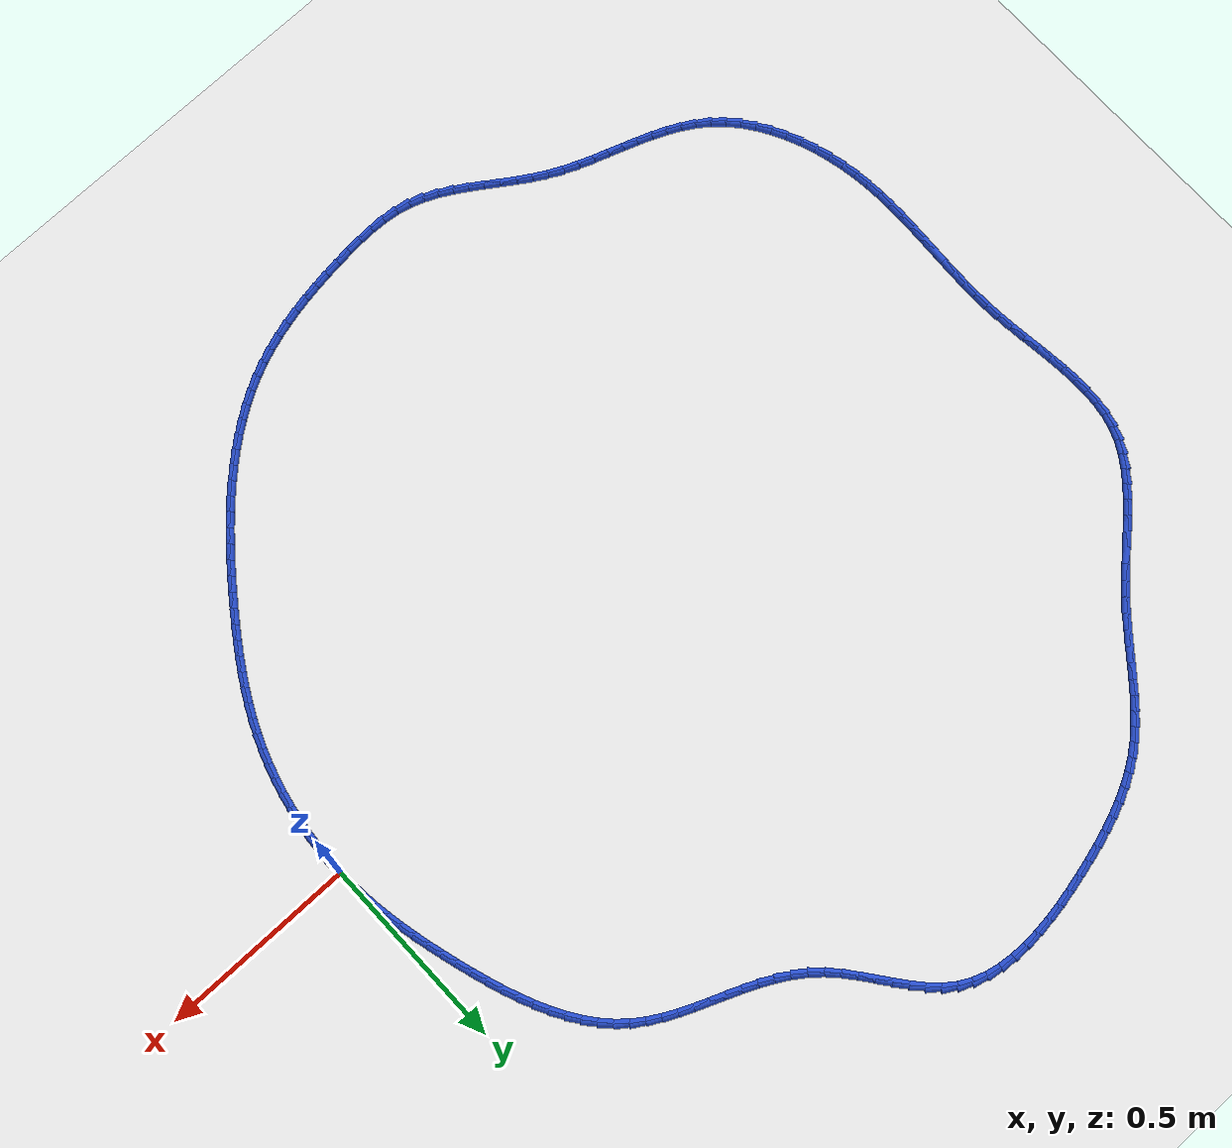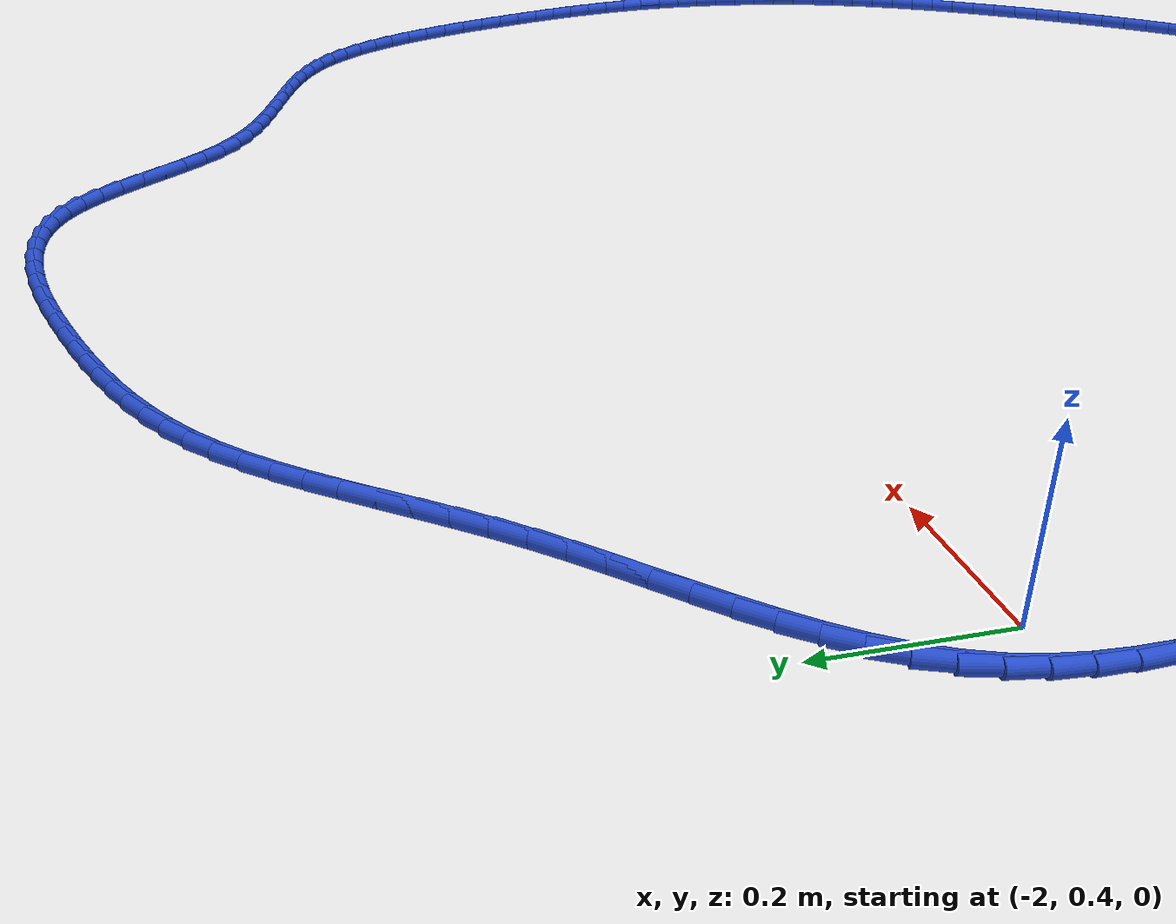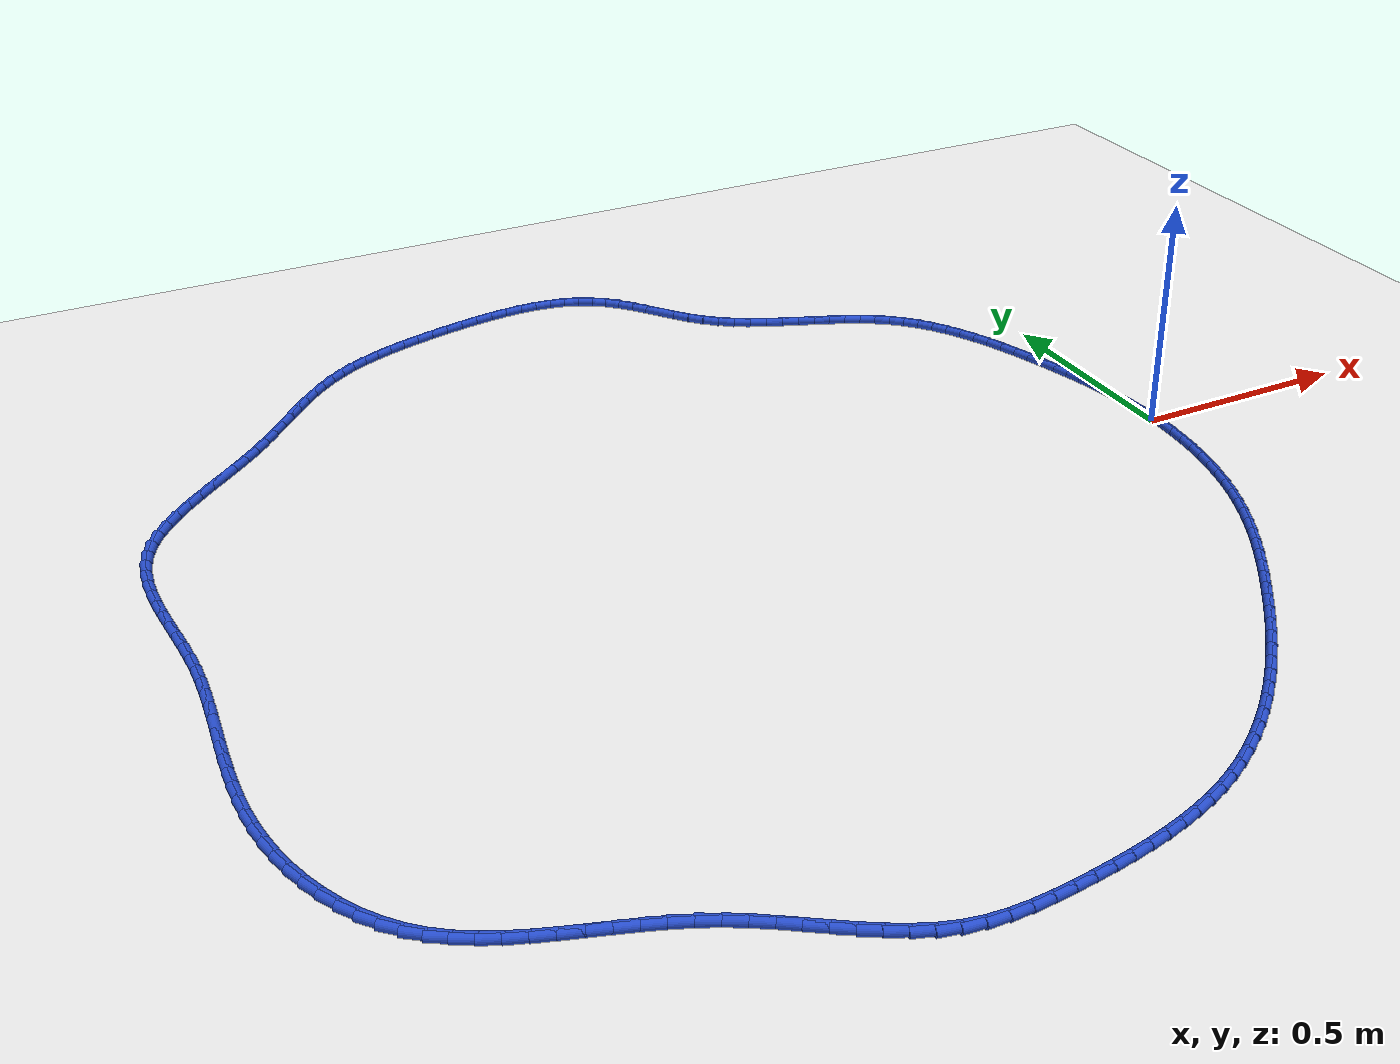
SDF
<sdf version="1.6">
 <world name="default">
  <light name="sun" type="directional">
   <pose>0 0 10 0 -0 0</pose>
   <diffuse>0.8 0.8 0.8 1</diffuse>
   <specular>0.2 0.2 0.2 1</specular>
   <attenuation>
    <range>1000</range>
    <constant>0.9</constant>
    <linear>0.01</linear>
    <quadratic>0.001</quadratic>
   </attenuation>
   <direction>-0.5 0.1 -0.9</direction>
  </light>
  <model name="ground_plane">
   <static>1</static>
   <link name="link">
    <collision name="collision">
     <geometry><plane><normal>0 0 1</normal><size>100 100</size></plane></geometry>
     <surface><friction><ode><mu>100</mu><mu2>50</mu2></ode></friction></surface>
    </collision>
    <visual name="visual">
     <cast_shadows>0</cast_shadows>
     <geometry><plane><normal>0 0 1</normal><size>100 100</size></plane></geometry>
     <material>
      <script><uri>file://media/materials/scripts/gazebo.material</uri><name>Gazebo/WhiteGlow</name></script>
     </material>
    </visual>
   </link>
  </model>
  <gravity>0 0 -9.8</gravity>
  <magnetic_field>6e-06 2.3e-05 -4.2e-05</magnetic_field>
  <atmosphere type="adiabatic"/>
  <physics name="default_physics" default="0" type="ode">
   <max_step_size>0.001</max_step_size>
   <real_time_factor>1</real_time_factor>
   <real_time_update_rate>1000</real_time_update_rate>
  </physics>
  <scene><ambient>0.4 0.4 0.4 1</ambient><background>0.7 0.7 0.7 1</background><shadows>1</shadows></scene>
  <spherical_coordinates>
   <surface_model>EARTH_WGS84</surface_model>
   <latitude_deg>0</latitude_deg>
   <longitude_deg>0</longitude_deg>
   <elevation>0</elevation>
   <heading_deg>0</heading_deg>
  </spherical_coordinates>
  <model name="line">
   <link name="link_0">
    <pose>-2.0816681711721685e-17 -1.0408340855860843e-16 0.01 0 1.57 -1.5327637463056027</pose>
    <collision name="collision">
     <geometry><cylinder><radius>0.01</radius><length>0.08</length></cylinder></geometry>
    </collision>
    <visual name="visual">
     <material>
      <script><name>Gazebo/Blue</name><uri>file://media/materials/scripts/gazebo.material</uri></script>
     </material>
     <geometry><cylinder><radius>0.01</radius><length>0.08</length></cylinder></geometry>
    </visual>
   </link>
   <link name="link_1">
    <pose>-0.001434148811461781 0.037690244482160684 0.01 0 1.57 -1.4921081020625393</pose>
    <collision name="collision">
     <geometry><cylinder><radius>0.01</radius><length>0.08</length></cylinder></geometry>
    </collision>
    <visual name="visual">
     <material>
      <script><name>Gazebo/Blue</name><uri>file://media/materials/scripts/gazebo.material</uri></script>
     </material>
     <geometry><cylinder><radius>0.01</radius><length>0.08</length></cylinder></geometry>
    </visual>
   </link>
   <link name="link_2">
    <pose>-0.004389834646771935 0.07517467053193923 0.01 0 1.57 -1.4542497640319472</pose>
    <collision name="collision">
     <geometry><cylinder><radius>0.01</radius><length>0.08</length></cylinder></geometry>
    </collision>
    <visual name="visual">
     <material>
      <script><name>Gazebo/Blue</name><uri>file://media/materials/scripts/gazebo.material</uri></script>
     </material>
     <geometry><cylinder><radius>0.01</radius><length>0.08</length></cylinder></geometry>
    </visual>
   </link>
   <link name="link_3">
    <pose>-0.008761367249101027 0.11251358094297098 0.01 0 1.57 -1.4194491700910916</pose>
    <collision name="collision">
     <geometry><cylinder><radius>0.01</radius><length>0.08</length></cylinder></geometry>
    </collision>
    <visual name="visual">
     <material>
      <script><name>Gazebo/Blue</name><uri>file://media/materials/scripts/gazebo.material</uri></script>
     </material>
     <geometry><cylinder><radius>0.01</radius><length>0.08</length></cylinder></geometry>
    </visual>
   </link>
   <link name="link_4">
    <pose>-0.014443056361619648 0.14976727850889157 0.01 0 1.57 -1.3878949564412437</pose>
    <collision name="collision">
     <geometry><cylinder><radius>0.01</radius><length>0.08</length></cylinder></geometry>
    </collision>
    <visual name="visual">
     <material>
      <script><name>Gazebo/Blue</name><uri>file://media/materials/scripts/gazebo.material</uri></script>
     </material>
     <geometry><cylinder><radius>0.01</radius><length>0.08</length></cylinder></geometry>
    </visual>
   </link>
   <link name="link_5">
    <pose>-0.021329211727498333 0.18699606602333635 0.01 0 1.57 -1.3597094110096877</pose>
    <collision name="collision">
     <geometry><cylinder><radius>0.01</radius><length>0.08</length></cylinder></geometry>
    </collision>
    <visual name="visual">
     <material>
      <script><name>Gazebo/Blue</name><uri>file://media/materials/scripts/gazebo.material</uri></script>
     </material>
     <geometry><cylinder><radius>0.01</radius><length>0.08</length></cylinder></geometry>
    </visual>
   </link>
   <link name="link_6">
    <pose>-0.029314143089907645 0.22426024627994096 0.01 0 1.57 -1.3349565964972274</pose>
    <collision name="collision">
     <geometry><cylinder><radius>0.01</radius><length>0.08</length></cylinder></geometry>
    </collision>
    <visual name="visual">
     <material>
      <script><name>Gazebo/Blue</name><uri>file://media/materials/scripts/gazebo.material</uri></script>
     </material>
     <geometry><cylinder><radius>0.01</radius><length>0.08</length></cylinder></geometry>
    </visual>
   </link>
   <link name="link_7">
    <pose>-0.03829216019201816 0.2616201220723408 0.01 0 1.57 -1.3136517567611161</pose>
    <collision name="collision">
     <geometry><cylinder><radius>0.01</radius><length>0.08</length></cylinder></geometry>
    </collision>
    <visual name="visual">
     <material>
      <script><name>Gazebo/Blue</name><uri>file://media/materials/scripts/gazebo.material</uri></script>
     </material>
     <geometry><cylinder><radius>0.01</radius><length>0.08</length></cylinder></geometry>
    </visual>
   </link>
   <link name="link_8">
    <pose>-0.048157572777000425 0.2991359961941715 0.01 0 1.57 -1.2957708750406254</pose>
    <collision name="collision">
     <geometry><cylinder><radius>0.01</radius><length>0.08</length></cylinder></geometry>
    </collision>
    <visual name="visual">
     <material>
      <script><name>Gazebo/Blue</name><uri>file://media/materials/scripts/gazebo.material</uri></script>
     </material>
     <geometry><cylinder><radius>0.01</radius><length>0.08</length></cylinder></geometry>
    </visual>
   </link>
   <link name="link_9">
    <pose>-0.058804690588024996 0.33686817143906855 0.01 0 1.57 -1.2802409625362063</pose>
    <collision name="collision">
     <geometry><cylinder><radius>0.01</radius><length>0.08</length></cylinder></geometry>
    </collision>
    <visual name="visual">
     <material>
      <script><name>Gazebo/Blue</name><uri>file://media/materials/scripts/gazebo.material</uri></script>
     </material>
     <geometry><cylinder><radius>0.01</radius><length>0.08</length></cylinder></geometry>
    </visual>
   </link>
   <link name="link_10">
    <pose>-0.07015812516088733 0.3748372760389036 0.01 0 1.57 -1.2608162352401373</pose>
    <collision name="collision">
     <geometry><cylinder><radius>0.01</radius><length>0.08</length></cylinder></geometry>
    </collision>
    <visual name="visual">
     <material>
      <script><name>Gazebo/Blue</name><uri>file://media/materials/scripts/gazebo.material</uri></script>
     </material>
     <geometry><cylinder><radius>0.01</radius><length>0.08</length></cylinder></geometry>
    </visual>
   </link>
   <link name="link_11">
    <pose>-0.0823255603847175 0.4128242390275658 0.01 0 1.57 -1.2349758218394293</pose>
    <collision name="collision">
     <geometry><cylinder><radius>0.01</radius><length>0.08</length></cylinder></geometry>
    </collision>
    <visual name="visual">
     <material>
      <script><name>Gazebo/Blue</name><uri>file://media/materials/scripts/gazebo.material</uri></script>
     </material>
     <geometry><cylinder><radius>0.01</radius><length>0.08</length></cylinder></geometry>
    </visual>
   </link>
   <link name="link_12">
    <pose>-0.09548308650301904 0.4505204240404468 0.01 0 1.57 -1.2023105526185576</pose>
    <collision name="collision">
     <geometry><cylinder><radius>0.01</radius><length>0.08</length></cylinder></geometry>
    </collision>
    <visual name="visual">
     <material>
      <script><name>Gazebo/Blue</name><uri>file://media/materials/scripts/gazebo.material</uri></script>
     </material>
     <geometry><cylinder><radius>0.01</radius><length>0.08</length></cylinder></geometry>
    </visual>
   </link>
   <link name="link_13">
    <pose>-0.10980691196875302 0.4876170399396394 0.01 0 1.57 -1.1622432033958452</pose>
    <collision name="collision">
     <geometry><cylinder><radius>0.01</radius><length>0.08</length></cylinder></geometry>
    </collision>
    <visual name="visual">
     <material>
      <script><name>Gazebo/Blue</name><uri>file://media/materials/scripts/gazebo.material</uri></script>
     </material>
     <geometry><cylinder><radius>0.01</radius><length>0.08</length></cylinder></geometry>
    </visual>
   </link>
   <link name="link_14">
    <pose>-0.12547324523488035 0.523805295587236 0.01 0 1.57 -1.114046624379047</pose>
    <collision name="collision">
     <geometry><cylinder><radius>0.01</radius><length>0.08</length></cylinder></geometry>
    </collision>
    <visual name="visual">
     <material>
      <script><name>Gazebo/Blue</name><uri>file://media/materials/scripts/gazebo.material</uri></script>
     </material>
     <geometry><cylinder><radius>0.01</radius><length>0.08</length></cylinder></geometry>
    </visual>
   </link>
   <link name="link_15">
    <pose>-0.14265829475436204 0.5587763998453292 0.01 0 1.57 -1.0568847860032085</pose>
    <collision name="collision">
     <geometry><cylinder><radius>0.01</radius><length>0.08</length></cylinder></geometry>
    </collision>
    <visual name="visual">
     <material>
      <script><name>Gazebo/Blue</name><uri>file://media/materials/scripts/gazebo.material</uri></script>
     </material>
     <geometry><cylinder><radius>0.01</radius><length>0.08</length></cylinder></geometry>
    </visual>
   </link>
   <link name="link_16">
    <pose>-0.16153826898015894 0.5922215615760117 0.01 0 1.57 -0.9898904217118326</pose>
    <collision name="collision">
     <geometry><cylinder><radius>0.01</radius><length>0.08</length></cylinder></geometry>
    </collision>
    <visual name="visual">
     <material>
      <script><name>Gazebo/Blue</name><uri>file://media/materials/scripts/gazebo.material</uri></script>
     </material>
     <geometry><cylinder><radius>0.01</radius><length>0.08</length></cylinder></geometry>
    </visual>
   </link>
   <link name="link_17">
    <pose>-0.18228937636523213 0.6238319896413755 0.01 0 1.57 -0.9123009492663512</pose>
    <collision name="collision">
     <geometry><cylinder><radius>0.01</radius><length>0.08</length></cylinder></geometry>
    </collision>
    <visual name="visual">
     <material>
      <script><name>Gazebo/Blue</name><uri>file://media/materials/scripts/gazebo.material</uri></script>
     </material>
     <geometry><cylinder><radius>0.01</radius><length>0.08</length></cylinder></geometry>
    </visual>
   </link>
   <link name="link_18">
    <pose>-0.2050878253625427 0.6532988929035142 0.01 0 1.57 -0.8236715274665197</pose>
    <collision name="collision">
     <geometry><cylinder><radius>0.01</radius><length>0.08</length></cylinder></geometry>
    </collision>
    <visual name="visual">
     <material>
      <script><name>Gazebo/Blue</name><uri>file://media/materials/scripts/gazebo.material</uri></script>
     </material>
     <geometry><cylinder><radius>0.01</radius><length>0.08</length></cylinder></geometry>
    </visual>
   </link>
   <link name="link_19">
    <pose>-0.2301098244250513 0.6803134802245194 0.01 0 1.57 -0.7241646192612321</pose>
    <collision name="collision">
     <geometry><cylinder><radius>0.01</radius><length>0.08</length></cylinder></geometry>
    </collision>
    <visual name="visual">
     <material>
      <script><name>Gazebo/Blue</name><uri>file://media/materials/scripts/gazebo.material</uri></script>
     </material>
     <geometry><cylinder><radius>0.01</radius><length>0.08</length></cylinder></geometry>
    </visual>
   </link>
   <link name="link_20">
    <pose>-0.25753155798945915 0.7045669944375058 0.01 0 1.57 -0.6206150540202744</pose>
    <collision name="collision">
     <geometry><cylinder><radius>0.01</radius><length>0.08</length></cylinder></geometry>
    </collision>
    <visual name="visual">
     <material>
      <script><name>Gazebo/Blue</name><uri>file://media/materials/scripts/gazebo.material</uri></script>
     </material>
     <geometry><cylinder><radius>0.01</radius><length>0.08</length></cylinder></geometry>
    </visual>
   </link>
   <link name="link_21">
    <pose>-0.2874072119640974 0.7259232454062835 0.01 0 1.57 -0.5337237370767031</pose>
    <collision name="collision">
     <geometry><cylinder><radius>0.01</radius><length>0.08</length></cylinder></geometry>
    </collision>
    <visual name="visual">
     <material>
      <script><name>Gazebo/Blue</name><uri>file://media/materials/scripts/gazebo.material</uri></script>
     </material>
     <geometry><cylinder><radius>0.01</radius><length>0.08</length></cylinder></geometry>
    </visual>
   </link>
   <link name="link_22">
    <pose>-0.3193852041308954 0.7448200023830225 0.01 0 1.57 -0.46772816997773464</pose>
    <collision name="collision">
     <geometry><cylinder><radius>0.01</radius><length>0.08</length></cylinder></geometry>
    </collision>
    <visual name="visual">
     <material>
      <script><name>Gazebo/Blue</name><uri>file://media/materials/scripts/gazebo.material</uri></script>
     </material>
     <geometry><cylinder><radius>0.01</radius><length>0.08</length></cylinder></geometry>
    </visual>
   </link>
   <link name="link_23">
    <pose>-0.35302969838057263 0.7618142118265774 0.01 0 1.57 -0.4217752783992592</pose>
    <collision name="collision">
     <geometry><cylinder><radius>0.01</radius><length>0.08</length></cylinder></geometry>
    </collision>
    <visual name="visual">
     <material>
      <script><name>Gazebo/Blue</name><uri>file://media/materials/scripts/gazebo.material</uri></script>
     </material>
     <geometry><cylinder><radius>0.01</radius><length>0.08</length></cylinder></geometry>
    </visual>
   </link>
   <link name="link_24">
    <pose>-0.38790485860384843 0.777462820195801 0.01 0 1.57 -0.39473039307191404</pose>
    <collision name="collision">
     <geometry><cylinder><radius>0.01</radius><length>0.08</length></cylinder></geometry>
    </collision>
    <visual name="visual">
     <material>
      <script><name>Gazebo/Blue</name><uri>file://media/materials/scripts/gazebo.material</uri></script>
     </material>
     <geometry><cylinder><radius>0.01</radius><length>0.08</length></cylinder></geometry>
    </visual>
   </link>
   <link name="link_25">
    <pose>-0.4235748486914429 0.7923227739495483 0.01 0 1.57 -0.3856794589711086</pose>
    <collision name="collision">
     <geometry><cylinder><radius>0.01</radius><length>0.08</length></cylinder></geometry>
    </collision>
    <visual name="visual">
     <material>
      <script><name>Gazebo/Blue</name><uri>file://media/materials/scripts/gazebo.material</uri></script>
     </material>
     <geometry><cylinder><radius>0.01</radius><length>0.08</length></cylinder></geometry>
    </visual>
   </link>
   <link name="link_26">
    <pose>-0.45960383253407533 0.8069510195466719 0.01 0 1.57 -0.3941611217867738</pose>
    <collision name="collision">
     <geometry><cylinder><radius>0.01</radius><length>0.08</length></cylinder></geometry>
    </collision>
    <visual name="visual">
     <material>
      <script><name>Gazebo/Blue</name><uri>file://media/materials/scripts/gazebo.material</uri></script>
     </material>
     <geometry><cylinder><radius>0.01</radius><length>0.08</length></cylinder></geometry>
    </visual>
   </link>
   <link name="link_27">
    <pose>-0.49555597402246543 0.8219045034460266 0.01 0 1.57 -0.42022058680894625</pose>
    <collision name="collision">
     <geometry><cylinder><radius>0.01</radius><length>0.08</length></cylinder></geometry>
    </collision>
    <visual name="visual">
     <material>
      <script><name>Gazebo/Blue</name><uri>file://media/materials/scripts/gazebo.material</uri></script>
     </material>
     <geometry><cylinder><radius>0.01</radius><length>0.08</length></cylinder></geometry>
    </visual>
   </link>
   <link name="link_28">
    <pose>-0.5309954370473328 0.8377401721064653 0.01 0 1.57 -0.46432757127431906</pose>
    <collision name="collision">
     <geometry><cylinder><radius>0.01</radius><length>0.08</length></cylinder></geometry>
    </collision>
    <visual name="visual">
     <material>
      <script><name>Gazebo/Blue</name><uri>file://media/materials/scripts/gazebo.material</uri></script>
     </material>
     <geometry><cylinder><radius>0.01</radius><length>0.08</length></cylinder></geometry>
    </visual>
   </link>
   <link name="link_29">
    <pose>-0.5654863854993971 0.8550149719868427 0.01 0 1.57 -0.5271430757725099</pose>
    <collision name="collision">
     <geometry><cylinder><radius>0.01</radius><length>0.08</length></cylinder></geometry>
    </collision>
    <visual name="visual">
     <material>
      <script><name>Gazebo/Blue</name><uri>file://media/materials/scripts/gazebo.material</uri></script>
     </material>
     <geometry><cylinder><radius>0.01</radius><length>0.08</length></cylinder></geometry>
    </visual>
   </link>
   <link name="link_30">
    <pose>-0.5985929832693777 0.8742858495460115 0.01 0 1.57 -0.6090811888094031</pose>
    <collision name="collision">
     <geometry><cylinder><radius>0.01</radius><length>0.08</length></cylinder></geometry>
    </collision>
    <visual name="visual">
     <material>
      <script><name>Gazebo/Blue</name><uri>file://media/materials/scripts/gazebo.material</uri></script>
     </material>
     <geometry><cylinder><radius>0.01</radius><length>0.08</length></cylinder></geometry>
    </visual>
   </link>
   <link name="link_31">
    <pose>-0.6298793942479946 0.8961097512428267 0.01 0 1.57 -0.7094021516972332</pose>
    <collision name="collision">
     <geometry><cylinder><radius>0.01</radius><length>0.08</length></cylinder></geometry>
    </collision>
    <visual name="visual">
     <material>
      <script><name>Gazebo/Blue</name><uri>file://media/materials/scripts/gazebo.material</uri></script>
     </material>
     <geometry><cylinder><radius>0.01</radius><length>0.08</length></cylinder></geometry>
    </visual>
   </link>
   <link name="link_32">
    <pose>-0.6589147795313913 0.921036329475355 0.01 0 1.57 -0.8089639535565651</pose>
    <collision name="collision">
     <geometry><cylinder><radius>0.01</radius><length>0.08</length></cylinder></geometry>
    </collision>
    <visual name="visual">
     <material>
      <script><name>Gazebo/Blue</name><uri>file://media/materials/scripts/gazebo.material</uri></script>
     </material>
     <geometry><cylinder><radius>0.01</radius><length>0.08</length></cylinder></geometry>
    </visual>
   </link>
   <link name="link_33">
    <pose>-0.6856483324062685 0.9490605310285759 0.01 0 1.57 -0.8786093852530055</pose>
    <collision name="collision">
     <geometry><cylinder><radius>0.01</radius><length>0.08</length></cylinder></geometry>
    </collision>
    <visual name="visual">
     <material>
      <script><name>Gazebo/Blue</name><uri>file://media/materials/scripts/gazebo.material</uri></script>
     </material>
     <geometry><cylinder><radius>0.01</radius><length>0.08</length></cylinder></geometry>
    </visual>
   </link>
   <link name="link_34">
    <pose>-0.7106697236635895 0.979242443811036 0.01 0 1.57 -0.9175937772902937</pose>
    <collision name="collision">
     <geometry><cylinder><radius>0.01</radius><length>0.08</length></cylinder></geometry>
    </collision>
    <visual name="visual">
     <material>
      <script><name>Gazebo/Blue</name><uri>file://media/materials/scripts/gazebo.material</uri></script>
     </material>
     <geometry><cylinder><radius>0.01</radius><length>0.08</length></cylinder></geometry>
    </visual>
   </link>
   <link name="link_35">
    <pose>-0.7346302014377316 1.0105522757188001 0.01 0 1.57 -0.927400305819622</pose>
    <collision name="collision">
     <geometry><cylinder><radius>0.01</radius><length>0.08</length></cylinder></geometry>
    </collision>
    <visual name="visual">
     <material>
      <script><name>Gazebo/Blue</name><uri>file://media/materials/scripts/gazebo.material</uri></script>
     </material>
     <geometry><cylinder><radius>0.01</radius><length>0.08</length></cylinder></geometry>
    </visual>
   </link>
   <link name="link_36">
    <pose>-0.7581810138630726 1.0419602346479329 0.01 0 1.57 -0.9079440865757169</pose>
    <collision name="collision">
     <geometry><cylinder><radius>0.01</radius><length>0.08</length></cylinder></geometry>
    </collision>
    <visual name="visual">
     <material>
      <script><name>Gazebo/Blue</name><uri>file://media/materials/scripts/gazebo.material</uri></script>
     </material>
     <geometry><cylinder><radius>0.01</radius><length>0.08</length></cylinder></geometry>
    </visual>
   </link>
   <link name="link_37">
    <pose>-0.7819734090739897 1.072436528494499 0.01 0 1.57 -0.8572592852688175</pose>
    <collision name="collision">
     <geometry><cylinder><radius>0.01</radius><length>0.08</length></cylinder></geometry>
    </collision>
    <visual name="visual">
     <material>
      <script><name>Gazebo/Blue</name><uri>file://media/materials/scripts/gazebo.material</uri></script>
     </material>
     <geometry><cylinder><radius>0.01</radius><length>0.08</length></cylinder></geometry>
    </visual>
   </link>
   <link name="link_38">
    <pose>-0.8066586352048603 1.100951365154563 0.01 0 1.57 -0.7717627114795786</pose>
    <collision name="collision">
     <geometry><cylinder><radius>0.01</radius><length>0.08</length></cylinder></geometry>
    </collision>
    <visual name="visual">
     <material>
      <script><name>Gazebo/Blue</name><uri>file://media/materials/scripts/gazebo.material</uri></script>
     </material>
     <geometry><cylinder><radius>0.01</radius><length>0.08</length></cylinder></geometry>
    </visual>
   </link>
   <link name="link_39">
    <pose>-0.8328879403900619 1.1264749525241897 0.01 0 1.57 -0.647632742397031</pose>
    <collision name="collision">
     <geometry><cylinder><radius>0.01</radius><length>0.08</length></cylinder></geometry>
    </collision>
    <visual name="visual">
     <material>
      <script><name>Gazebo/Blue</name><uri>file://media/materials/scripts/gazebo.material</uri></script>
     </material>
     <geometry><cylinder><radius>0.01</radius><length>0.08</length></cylinder></geometry>
    </visual>
   </link>
   <link name="link_40">
    <pose>-0.8613125727639719 1.147977498499444 0.01 0 1.57 -0.4924002176386117</pose>
    <collision name="collision">
     <geometry><cylinder><radius>0.01</radius><length>0.08</length></cylinder></geometry>
    </collision>
    <visual name="visual">
     <material>
      <script><name>Gazebo/Blue</name><uri>file://media/materials/scripts/gazebo.material</uri></script>
     </material>
     <geometry><cylinder><radius>0.01</radius><length>0.08</length></cylinder></geometry>
    </visual>
   </link>
   <link name="link_41">
    <pose>-0.8924196567085617 1.1646656773094157 0.01 0 1.57 -0.34451761371591727</pose>
    <collision name="collision">
     <geometry><cylinder><radius>0.01</radius><length>0.08</length></cylinder></geometry>
    </collision>
    <visual name="visual">
     <material>
      <script><name>Gazebo/Blue</name><uri>file://media/materials/scripts/gazebo.material</uri></script>
     </material>
     <geometry><cylinder><radius>0.01</radius><length>0.08</length></cylinder></geometry>
    </visual>
   </link>
   <link name="link_42">
    <pose>-0.9260189817068025 1.176722054225465 0.01 0 1.57 -0.21652344081053565</pose>
    <collision name="collision">
     <geometry><cylinder><radius>0.01</radius><length>0.08</length></cylinder></geometry>
    </collision>
    <visual name="visual">
     <material>
      <script><name>Gazebo/Blue</name><uri>file://media/materials/scripts/gazebo.material</uri></script>
     </material>
     <geometry><cylinder><radius>0.01</radius><length>0.08</length></cylinder></geometry>
    </visual>
   </link>
   <link name="link_43">
    <pose>-0.9617456292186104 1.1845809104647338 0.01 0 1.57 -0.10881680400815058</pose>
    <collision name="collision">
     <geometry><cylinder><radius>0.01</radius><length>0.08</length></cylinder></geometry>
    </collision>
    <visual name="visual">
     <material>
      <script><name>Gazebo/Blue</name><uri>file://media/materials/scripts/gazebo.material</uri></script>
     </material>
     <geometry><cylinder><radius>0.01</radius><length>0.08</length></cylinder></geometry>
    </visual>
   </link>
   <link name="link_44">
    <pose>-0.9992346805124975 1.188676527520133 0.01 0 1.57 -0.01971273679869438</pose>
    <collision name="collision">
     <geometry><cylinder><radius>0.01</radius><length>0.08</length></cylinder></geometry>
    </collision>
    <visual name="visual">
     <material>
      <script><name>Gazebo/Blue</name><uri>file://media/materials/scripts/gazebo.material</uri></script>
     </material>
     <geometry><cylinder><radius>0.01</radius><length>0.08</length></cylinder></geometry>
    </visual>
   </link>
   <link name="link_45">
    <pose>-1.0381212168569767 1.1894431868845738 0.01 0 1.57 0.05325782257838895</pose>
    <collision name="collision">
     <geometry><cylinder><radius>0.01</radius><length>0.08</length></cylinder></geometry>
    </collision>
    <visual name="visual">
     <material>
      <script><name>Gazebo/Blue</name><uri>file://media/materials/scripts/gazebo.material</uri></script>
     </material>
     <geometry><cylinder><radius>0.01</radius><length>0.08</length></cylinder></geometry>
    </visual>
   </link>
   <link name="link_46">
    <pose>-1.078040319520561 1.1873151700509688 0.01 0 1.57 0.11257398742156893</pose>
    <collision name="collision">
     <geometry><cylinder><radius>0.01</radius><length>0.08</length></cylinder></geometry>
    </collision>
    <visual name="visual">
     <material>
      <script><name>Gazebo/Blue</name><uri>file://media/materials/scripts/gazebo.material</uri></script>
     </material>
     <geometry><cylinder><radius>0.01</radius><length>0.08</length></cylinder></geometry>
    </visual>
   </link>
   <link name="link_47">
    <pose>-1.1186270697717626 1.182726758512229 0.01 0 1.57 0.16037664011778482</pose>
    <collision name="collision">
     <geometry><cylinder><radius>0.01</radius><length>0.08</length></cylinder></geometry>
    </collision>
    <visual name="visual">
     <material>
      <script><name>Gazebo/Blue</name><uri>file://media/materials/scripts/gazebo.material</uri></script>
     </material>
     <geometry><cylinder><radius>0.01</radius><length>0.08</length></cylinder></geometry>
    </visual>
   </link>
   <link name="link_48">
    <pose>-1.159516548879094 1.1761122337612646 0.01 0 1.57 0.19835859251996052</pose>
    <collision name="collision">
     <geometry><cylinder><radius>0.01</radius><length>0.08</length></cylinder></geometry>
    </collision>
    <visual name="visual">
     <material>
      <script><name>Gazebo/Blue</name><uri>file://media/materials/scripts/gazebo.material</uri></script>
     </material>
     <geometry><cylinder><radius>0.01</radius><length>0.08</length></cylinder></geometry>
    </visual>
   </link>
   <link name="link_49">
    <pose>-1.2003438381110687 1.1679058772909883 0.01 0 1.57 0.22775719018973978</pose>
    <collision name="collision">
     <geometry><cylinder><radius>0.01</radius><length>0.08</length></cylinder></geometry>
    </collision>
    <visual name="visual">
     <material>
      <script><name>Gazebo/Blue</name><uri>file://media/materials/scripts/gazebo.material</uri></script>
     </material>
     <geometry><cylinder><radius>0.01</radius><length>0.08</length></cylinder></geometry>
    </visual>
   </link>
   <link name="link_50">
    <pose>-1.2407440187361982 1.1585419705943107 0.01 0 1.57 0.25022045598949655</pose>
    <collision name="collision">
     <geometry><cylinder><radius>0.01</radius><length>0.08</length></cylinder></geometry>
    </collision>
    <visual name="visual">
     <material>
      <script><name>Gazebo/Blue</name><uri>file://media/materials/scripts/gazebo.material</uri></script>
     </material>
     <geometry><cylinder><radius>0.01</radius><length>0.08</length></cylinder></geometry>
    </visual>
   </link>
   <link name="link_51">
    <pose>-1.2803678609756328 1.1484150372153858 0.01 0 1.57 0.27448541488182415</pose>
    <collision name="collision">
     <geometry><cylinder><radius>0.01</radius><length>0.08</length></cylinder></geometry>
    </collision>
    <visual name="visual">
     <material>
      <script><name>Gazebo/Blue</name><uri>file://media/materials/scripts/gazebo.material</uri></script>
     </material>
     <geometry><cylinder><radius>0.01</radius><length>0.08</length></cylinder></geometry>
    </visual>
   </link>
   <link name="link_52">
    <pose>-1.319019478860041 1.1375310065415483 0.01 0 1.57 0.30565145141745476</pose>
    <collision name="collision">
     <geometry><cylinder><radius>0.01</radius><length>0.08</length></cylinder></geometry>
    </collision>
    <visual name="visual">
     <material>
      <script><name>Gazebo/Blue</name><uri>file://media/materials/scripts/gazebo.material</uri></script>
     </material>
     <geometry><cylinder><radius>0.01</radius><length>0.08</length></cylinder></geometry>
    </visual>
   </link>
   <link name="link_53">
    <pose>-1.3565896739133052 1.125676130012661 0.01 0 1.57 0.3442156234422525</pose>
    <collision name="collision">
     <geometry><cylinder><radius>0.01</radius><length>0.08</length></cylinder></geometry>
    </collision>
    <visual name="visual">
     <material>
      <script><name>Gazebo/Blue</name><uri>file://media/materials/scripts/gazebo.material</uri></script>
     </material>
     <geometry><cylinder><radius>0.01</radius><length>0.08</length></cylinder></geometry>
    </visual>
   </link>
   <link name="link_54">
    <pose>-1.392970230092997 1.1126341694474453 0.01 0 1.57 0.39059399532635397</pose>
    <collision name="collision">
     <geometry><cylinder><radius>0.01</radius><length>0.08</length></cylinder></geometry>
    </collision>
    <visual name="visual">
     <material>
      <script><name>Gazebo/Blue</name><uri>file://media/materials/scripts/gazebo.material</uri></script>
     </material>
     <geometry><cylinder><radius>0.01</radius><length>0.08</length></cylinder></geometry>
    </visual>
   </link>
   <link name="link_55">
    <pose>-1.4280529313566865 1.0981888866646217 0.01 0 1.57 0.44510527132764954</pose>
    <collision name="collision">
     <geometry><cylinder><radius>0.01</radius><length>0.08</length></cylinder></geometry>
    </collision>
    <visual name="visual">
     <material>
      <script><name>Gazebo/Blue</name><uri>file://media/materials/scripts/gazebo.material</uri></script>
     </material>
     <geometry><cylinder><radius>0.01</radius><length>0.08</length></cylinder></geometry>
    </visual>
   </link>
   <link name="link_56">
    <pose>-1.4617295616619441 1.0821240434829122 0.01 0 1.57 0.5078744594809679</pose>
    <collision name="collision">
     <geometry><cylinder><radius>0.01</radius><length>0.08</length></cylinder></geometry>
    </collision>
    <visual name="visual">
     <material>
      <script><name>Gazebo/Blue</name><uri>file://media/materials/scripts/gazebo.material</uri></script>
     </material>
     <geometry><cylinder><radius>0.01</radius><length>0.08</length></cylinder></geometry>
    </visual>
   </link>
   <link name="link_57">
    <pose>-1.4938919049663402 1.0642234017210381 0.01 0 1.57 0.5787145521718183</pose>
    <collision name="collision">
     <geometry><cylinder><radius>0.01</radius><length>0.08</length></cylinder></geometry>
    </collision>
    <visual name="visual">
     <material>
      <script><name>Gazebo/Blue</name><uri>file://media/materials/scripts/gazebo.material</uri></script>
     </material>
     <geometry><cylinder><radius>0.01</radius><length>0.08</length></cylinder></geometry>
    </visual>
   </link>
   <link name="link_58">
    <pose>-1.5244317452274454 1.0442707231977202 0.01 0 1.57 0.6561608870835796</pose>
    <collision name="collision">
     <geometry><cylinder><radius>0.01</radius><length>0.08</length></cylinder></geometry>
    </collision>
    <visual name="visual">
     <material>
      <script><name>Gazebo/Blue</name><uri>file://media/materials/scripts/gazebo.material</uri></script>
     </material>
     <geometry><cylinder><radius>0.01</radius><length>0.08</length></cylinder></geometry>
    </visual>
   </link>
   <link name="link_59">
    <pose>-1.553260004145151 1.022073782624647 0.01 0 1.57 0.7283613619042232</pose>
    <collision name="collision">
     <geometry><cylinder><radius>0.01</radius><length>0.08</length></cylinder></geometry>
    </collision>
    <visual name="visual">
     <material>
      <script><name>Gazebo/Blue</name><uri>file://media/materials/scripts/gazebo.material</uri></script>
     </material>
     <geometry><cylinder><radius>0.01</radius><length>0.08</length></cylinder></geometry>
    </visual>
   </link>
   <link name="link_60">
    <pose>-1.5805324416438782 0.9977475630550663 0.01 0 1.57 0.7870557928596922</pose>
    <collision name="collision">
     <geometry><cylinder><radius>0.01</radius><length>0.08</length></cylinder></geometry>
    </collision>
    <visual name="visual">
     <material>
      <script><name>Gazebo/Blue</name><uri>file://media/materials/scripts/gazebo.material</uri></script>
     </material>
     <geometry><cylinder><radius>0.01</radius><length>0.08</length></cylinder></geometry>
    </visual>
   </link>
   <link name="link_61">
    <pose>-1.6065740882779331 0.971619438191532 0.01 0 1.57 0.8319944187781226</pose>
    <collision name="collision">
     <geometry><cylinder><radius>0.01</radius><length>0.08</length></cylinder></geometry>
    </collision>
    <visual name="visual">
     <material>
      <script><name>Gazebo/Blue</name><uri>file://media/materials/scripts/gazebo.material</uri></script>
     </material>
     <geometry><cylinder><radius>0.01</radius><length>0.08</length></cylinder></geometry>
    </visual>
   </link>
   <link name="link_62">
    <pose>-1.6317133504019103 0.944021017488631 0.01 0 1.57 0.8635060251961109</pose>
    <collision name="collision">
     <geometry><cylinder><radius>0.01</radius><length>0.08</length></cylinder></geometry>
    </collision>
    <visual name="visual">
     <material>
      <script><name>Gazebo/Blue</name><uri>file://media/materials/scripts/gazebo.material</uri></script>
     </material>
     <geometry><cylinder><radius>0.01</radius><length>0.08</length></cylinder></geometry>
    </visual>
   </link>
   <link name="link_63">
    <pose>-1.6562786343704052 0.9152839104009517 0.01 0 1.57 0.8820896477272588</pose>
    <collision name="collision">
     <geometry><cylinder><radius>0.01</radius><length>0.08</length></cylinder></geometry>
    </collision>
    <visual name="visual">
     <material>
      <script><name>Gazebo/Blue</name><uri>file://media/materials/scripts/gazebo.material</uri></script>
     </material>
     <geometry><cylinder><radius>0.01</radius><length>0.08</length></cylinder></geometry>
    </visual>
   </link>
   <link name="link_64">
    <pose>-1.6805983465380099 0.8857397263830826 0.01 0 1.57 0.8882474621012977</pose>
    <collision name="collision">
     <geometry><cylinder><radius>0.01</radius><length>0.08</length></cylinder></geometry>
    </collision>
    <visual name="visual">
     <material>
      <script><name>Gazebo/Blue</name><uri>file://media/materials/scripts/gazebo.material</uri></script>
     </material>
     <geometry><cylinder><radius>0.01</radius><length>0.08</length></cylinder></geometry>
    </visual>
   </link>
   <link name="link_65">
    <pose>-1.7050008932593208 0.8557200748896113 0.01 0 1.57 0.882400603885393</pose>
    <collision name="collision">
     <geometry><cylinder><radius>0.01</radius><length>0.08</length></cylinder></geometry>
    </collision>
    <visual name="visual">
     <material>
      <script><name>Gazebo/Blue</name><uri>file://media/materials/scripts/gazebo.material</uri></script>
     </material>
     <geometry><cylinder><radius>0.01</radius><length>0.08</length></cylinder></geometry>
    </visual>
   </link>
   <link name="link_66">
    <pose>-1.7298146808889314 0.8255565653751253 0.01 0 1.57 0.8648700391980358</pose>
    <collision name="collision">
     <geometry><cylinder><radius>0.01</radius><length>0.08</length></cylinder></geometry>
    </collision>
    <visual name="visual">
     <material>
      <script><name>Gazebo/Blue</name><uri>file://media/materials/scripts/gazebo.material</uri></script>
     </material>
     <geometry><cylinder><radius>0.01</radius><length>0.08</length></cylinder></geometry>
    </visual>
   </link>
   <link name="link_67">
    <pose>-1.7553681157814363 0.7955808072942137 0.01 0 1.57 0.835908223971081</pose>
    <collision name="collision">
     <geometry><cylinder><radius>0.01</radius><length>0.08</length></cylinder></geometry>
    </collision>
    <visual name="visual">
     <material>
      <script><name>Gazebo/Blue</name><uri>file://media/materials/scripts/gazebo.material</uri></script>
     </material>
     <geometry><cylinder><radius>0.01</radius><length>0.08</length></cylinder></geometry>
    </visual>
   </link>
   <link name="link_68">
    <pose>-1.7819896042914296 0.7661244101014637 0.01 0 1.57 0.7986590974441794</pose>
    <collision name="collision">
     <geometry><cylinder><radius>0.01</radius><length>0.08</length></cylinder></geometry>
    </collision>
    <visual name="visual">
     <material>
      <script><name>Gazebo/Blue</name><uri>file://media/materials/scripts/gazebo.material</uri></script>
     </material>
     <geometry><cylinder><radius>0.01</radius><length>0.08</length></cylinder></geometry>
    </visual>
   </link>
   <link name="link_69">
    <pose>-1.809909153456773 0.737454386350517 0.01 0 1.57 0.7696715150609269</pose>
    <collision name="collision">
     <geometry><cylinder><radius>0.01</radius><length>0.08</length></cylinder></geometry>
    </collision>
    <visual name="visual">
     <material>
      <script><name>Gazebo/Blue</name><uri>file://media/materials/scripts/gazebo.material</uri></script>
     </material>
     <geometry><cylinder><radius>0.01</radius><length>0.08</length></cylinder></geometry>
    </visual>
   </link>
   <link name="link_70">
    <pose>-1.8387913955834743 0.7094665930142284 0.01 0 1.57 0.7543436629798846</pose>
    <collision name="collision">
     <geometry><cylinder><radius>0.01</radius><length>0.08</length></cylinder></geometry>
    </collision>
    <visual name="visual">
     <material>
      <script><name>Gazebo/Blue</name><uri>file://media/materials/scripts/gazebo.material</uri></script>
     </material>
     <geometry><cylinder><radius>0.01</radius><length>0.08</length></cylinder></geometry>
    </visual>
   </link>
   <link name="link_71">
    <pose>-1.8680994243627893 0.6819245815742532 0.01 0 1.57 0.7524393383066788</pose>
    <collision name="collision">
     <geometry><cylinder><radius>0.01</radius><length>0.08</length></cylinder></geometry>
    </collision>
    <visual name="visual">
     <material>
      <script><name>Gazebo/Blue</name><uri>file://media/materials/scripts/gazebo.material</uri></script>
     </material>
     <geometry><cylinder><radius>0.01</radius><length>0.08</length></cylinder></geometry>
    </visual>
   </link>
   <link name="link_72">
    <pose>-1.8972960858764154 0.6545917409622357 0.01 0 1.57 0.7641548379477962</pose>
    <collision name="collision">
     <geometry><cylinder><radius>0.01</radius><length>0.08</length></cylinder></geometry>
    </collision>
    <visual name="visual">
     <material>
      <script><name>Gazebo/Blue</name><uri>file://media/materials/scripts/gazebo.material</uri></script>
     </material>
     <geometry><cylinder><radius>0.01</radius><length>0.08</length></cylinder></geometry>
    </visual>
   </link>
   <link name="link_73">
    <pose>-1.9258442262060511 0.6272314601098192 0.01 0 1.57 0.7901604875656398</pose>
    <collision name="collision">
     <geometry><cylinder><radius>0.01</radius><length>0.08</length></cylinder></geometry>
    </collision>
    <visual name="visual">
     <material>
      <script><name>Gazebo/Blue</name><uri>file://media/materials/scripts/gazebo.material</uri></script>
     </material>
     <geometry><cylinder><radius>0.01</radius><length>0.08</length></cylinder></geometry>
    </visual>
   </link>
   <link name="link_74">
    <pose>-1.9532066914333943 0.5996071279486477 0.01 0 1.57 0.8315919201613304</pose>
    <collision name="collision">
     <geometry><cylinder><radius>0.01</radius><length>0.08</length></cylinder></geometry>
    </collision>
    <visual name="visual">
     <material>
      <script><name>Gazebo/Blue</name><uri>file://media/materials/scripts/gazebo.material</uri></script>
     </material>
     <geometry><cylinder><radius>0.01</radius><length>0.08</length></cylinder></geometry>
    </visual>
   </link>
   <link name="link_75">
    <pose>-1.9788463276401418 0.5714821334103654 0.01 0 1.57 0.8899620542298988</pose>
    <collision name="collision">
     <geometry><cylinder><radius>0.01</radius><length>0.08</length></cylinder></geometry>
    </collision>
    <visual name="visual">
     <material>
      <script><name>Gazebo/Blue</name><uri>file://media/materials/scripts/gazebo.material</uri></script>
     </material>
     <geometry><cylinder><radius>0.01</radius><length>0.08</length></cylinder></geometry>
    </visual>
   </link>
   <link name="link_76">
    <pose>-2.002225980907993 0.542619865426616 0.01 0 1.57 0.9669139163180537</pose>
    <collision name="collision">
     <geometry><cylinder><radius>0.01</radius><length>0.08</length></cylinder></geometry>
    </collision>
    <visual name="visual">
     <material>
      <script><name>Gazebo/Blue</name><uri>file://media/materials/scripts/gazebo.material</uri></script>
     </material>
     <geometry><cylinder><radius>0.01</radius><length>0.08</length></cylinder></geometry>
    </visual>
   </link>
   <link name="link_77">
    <pose>-2.022808497318645 0.5127837129290429 0.01 0 1.57 1.063695661062746</pose>
    <collision name="collision">
     <geometry><cylinder><radius>0.01</radius><length>0.08</length></cylinder></geometry>
    </collision>
    <visual name="visual">
     <material>
      <script><name>Gazebo/Blue</name><uri>file://media/materials/scripts/gazebo.material</uri></script>
     </material>
     <geometry><cylinder><radius>0.01</radius><length>0.08</length></cylinder></geometry>
    </visual>
   </link>
   <link name="link_78">
    <pose>-2.0400567229537954 0.48173706484929063 0.01 0 1.57 1.180214312019721</pose>
    <collision name="collision">
     <geometry><cylinder><radius>0.01</radius><length>0.08</length></cylinder></geometry>
    </collision>
    <visual name="visual">
     <material>
      <script><name>Gazebo/Blue</name><uri>file://media/materials/scripts/gazebo.material</uri></script>
     </material>
     <geometry><cylinder><radius>0.01</radius><length>0.08</length></cylinder></geometry>
    </visual>
   </link>
   <link name="link_79">
    <pose>-2.053435265761804 0.44924400810427356 0.01 0 1.57 1.3044693716685836</pose>
    <collision name="collision">
     <geometry><cylinder><radius>0.01</radius><length>0.08</length></cylinder></geometry>
    </collision>
    <visual name="visual">
     <material>
      <script><name>Gazebo/Blue</name><uri>file://media/materials/scripts/gazebo.material</uri></script>
     </material>
     <geometry><cylinder><radius>0.01</radius><length>0.08</length></cylinder></geometry>
    </visual>
   </link>
   <link name="link_80">
    <pose>-2.0627244522830046 0.4151937054362903 0.01 0 1.57 1.412522554717471</pose>
    <collision name="collision">
     <geometry><cylinder><radius>0.01</radius><length>0.08</length></cylinder></geometry>
    </collision>
    <visual name="visual">
     <material>
      <script><name>Gazebo/Blue</name><uri>file://media/materials/scripts/gazebo.material</uri></script>
     </material>
     <geometry><cylinder><radius>0.01</radius><length>0.08</length></cylinder></geometry>
    </visual>
   </link>
   <link name="link_81">
    <pose>-2.068382552778238 0.37974389537811276 0.01 0 1.57 1.5007183481354398</pose>
    <collision name="collision">
     <geometry><cylinder><radius>0.01</radius><length>0.08</length></cylinder></geometry>
    </collision>
    <visual name="visual">
     <material>
      <script><name>Gazebo/Blue</name><uri>file://media/materials/scripts/gazebo.material</uri></script>
     </material>
     <geometry><cylinder><radius>0.01</radius><length>0.08</length></cylinder></geometry>
    </visual>
   </link>
   <link name="link_82">
    <pose>-2.0709556013346364 0.343087085187862 0.01 0 1.57 1.5698929681991656</pose>
    <collision name="collision">
     <geometry><cylinder><radius>0.01</radius><length>0.08</length></cylinder></geometry>
    </collision>
    <visual name="visual">
     <material>
      <script><name>Gazebo/Blue</name><uri>file://media/materials/scripts/gazebo.material</uri></script>
     </material>
     <geometry><cylinder><radius>0.01</radius><length>0.08</length></cylinder></geometry>
    </visual>
   </link>
   <link name="link_83">
    <pose>-2.070989632039329 0.30541578212365894 0.01 0 1.57 -1.5199494232117647</pose>
    <collision name="collision">
     <geometry><cylinder><radius>0.01</radius><length>0.08</length></cylinder></geometry>
    </collision>
    <visual name="visual">
     <material>
      <script><name>Gazebo/Blue</name><uri>file://media/materials/scripts/gazebo.material</uri></script>
     </material>
     <geometry><cylinder><radius>0.01</radius><length>0.08</length></cylinder></geometry>
    </visual>
   </link>
   <link name="link_84">
    <pose>-2.0690306789794493 0.2669224934436255 0.01 0 1.57 -1.4839584675421924</pose>
    <collision name="collision">
     <geometry><cylinder><radius>0.01</radius><length>0.08</length></cylinder></geometry>
    </collision>
    <visual name="visual">
     <material>
      <script><name>Gazebo/Blue</name><uri>file://media/materials/scripts/gazebo.material</uri></script>
     </material>
     <geometry><cylinder><radius>0.01</radius><length>0.08</length></cylinder></geometry>
    </visual>
   </link>
   <link name="link_85">
    <pose>-2.0656247762421285 0.22779972640588225 0.01 0 1.57 -1.4623546853439038</pose>
    <collision name="collision">
     <geometry><cylinder><radius>0.01</radius><length>0.08</length></cylinder></geometry>
    </collision>
    <visual name="visual">
     <material>
      <script><name>Gazebo/Blue</name><uri>file://media/materials/scripts/gazebo.material</uri></script>
     </material>
     <geometry><cylinder><radius>0.01</radius><length>0.08</length></cylinder></geometry>
    </visual>
   </link>
   <link name="link_86">
    <pose>-2.0613179579144973 0.18823998826855123 0.01 0 1.57 -1.4542116485671366</pose>
    <collision name="collision">
     <geometry><cylinder><radius>0.01</radius><length>0.08</length></cylinder></geometry>
    </collision>
    <visual name="visual">
     <material>
      <script><name>Gazebo/Blue</name><uri>file://media/materials/scripts/gazebo.material</uri></script>
     </material>
     <geometry><cylinder><radius>0.01</radius><length>0.08</length></cylinder></geometry>
    </visual>
   </link>
   <link name="link_87">
    <pose>-2.0566562580836885 0.1484357862897533 0.01 0 1.57 -1.4590961772638547</pose>
    <collision name="collision">
     <geometry><cylinder><radius>0.01</radius><length>0.08</length></cylinder></geometry>
    </collision>
    <visual name="visual">
     <material>
      <script><name>Gazebo/Blue</name><uri>file://media/materials/scripts/gazebo.material</uri></script>
     </material>
     <geometry><cylinder><radius>0.01</radius><length>0.08</length></cylinder></geometry>
    </visual>
   </link>
   <link name="link_88">
    <pose>-2.0521857108368318 0.10857962772760929 0.01 0 1.57 -1.4770693975414164</pose>
    <collision name="collision">
     <geometry><cylinder><radius>0.01</radius><length>0.08</length></cylinder></geometry>
    </collision>
    <visual name="visual">
     <material>
      <script><name>Gazebo/Blue</name><uri>file://media/materials/scripts/gazebo.material</uri></script>
     </material>
     <geometry><cylinder><radius>0.01</radius><length>0.08</length></cylinder></geometry>
    </visual>
   </link>
   <link name="link_89">
    <pose>-2.0484523502610594 0.06886401984024126 0.01 0 1.57 -1.508317831723412</pose>
    <collision name="collision">
     <geometry><cylinder><radius>0.01</radius><length>0.08</length></cylinder></geometry>
    </collision>
    <visual name="visual">
     <material>
      <script><name>Gazebo/Blue</name><uri>file://media/materials/scripts/gazebo.material</uri></script>
     </material>
     <geometry><cylinder><radius>0.01</radius><length>0.08</length></cylinder></geometry>
    </visual>
   </link>
   <link name="link_90">
    <pose>-2.0459883268093058 0.029477404367561195 0.01 0 1.57 -1.54402767362524</pose>
    <collision name="collision">
     <geometry><cylinder><radius>0.01</radius><length>0.08</length></cylinder></geometry>
    </collision>
    <visual name="visual">
     <material>
      <script><name>Gazebo/Blue</name><uri>file://media/materials/scripts/gazebo.material</uri></script>
     </material>
     <geometry><cylinder><radius>0.01</radius><length>0.08</length></cylinder></geometry>
    </visual>
   </link>
   <link name="link_91">
    <pose>-2.0449446139701166 -0.009503396276370861 0.01 0 1.57 1.567987165825125</pose>
    <collision name="collision">
     <geometry><cylinder><radius>0.01</radius><length>0.08</length></cylinder></geometry>
    </collision>
    <visual name="visual">
     <material>
      <script><name>Gazebo/Blue</name><uri>file://media/materials/scripts/gazebo.material</uri></script>
     </material>
     <geometry><cylinder><radius>0.01</radius><length>0.08</length></cylinder></geometry>
    </visual>
   </link>
   <link name="link_92">
    <pose>-2.045053106528209 -0.04812427769765665 0.01 0 1.57 1.5454551702174715</pose>
    <collision name="collision">
     <geometry><cylinder><radius>0.01</radius><length>0.08</length></cylinder></geometry>
    </collision>
    <visual name="visual">
     <material>
      <script><name>Gazebo/Blue</name><uri>file://media/materials/scripts/gazebo.material</uri></script>
     </material>
     <geometry><cylinder><radius>0.01</radius><length>0.08</length></cylinder></geometry>
    </visual>
   </link>
   <link name="link_93">
    <pose>-2.0460242139262927 -0.08643742701425138 0.01 0 1.57 1.5302450303805055</pose>
    <collision name="collision">
     <geometry><cylinder><radius>0.01</radius><length>0.08</length></cylinder></geometry>
    </collision>
    <visual name="visual">
     <material>
      <script><name>Gazebo/Blue</name><uri>file://media/materials/scripts/gazebo.material</uri></script>
     </material>
     <geometry><cylinder><radius>0.01</radius><length>0.08</length></cylinder></geometry>
    </visual>
   </link>
   <link name="link_94">
    <pose>-2.047568345607075 -0.12449503134411263 0.01 0 1.57 1.522554778622991</pose>
    <collision name="collision">
     <geometry><cylinder><radius>0.01</radius><length>0.08</length></cylinder></geometry>
    </collision>
    <visual name="visual">
     <material>
      <script><name>Gazebo/Blue</name><uri>file://media/materials/scripts/gazebo.material</uri></script>
     </material>
     <geometry><cylinder><radius>0.01</radius><length>0.08</length></cylinder></geometry>
    </visual>
   </link>
   <link name="link_95">
    <pose>-2.0493959110132662 -0.16234927780519717 0.01 0 1.57 1.5225245719226421</pose>
    <collision name="collision">
     <geometry><cylinder><radius>0.01</radius><length>0.08</length></cylinder></geometry>
    </collision>
    <visual name="visual">
     <material>
      <script><name>Gazebo/Blue</name><uri>file://media/materials/scripts/gazebo.material</uri></script>
     </material>
     <geometry><cylinder><radius>0.01</radius><length>0.08</length></cylinder></geometry>
    </visual>
   </link>
   <link name="link_96">
    <pose>-2.051217319587576 -0.20005235351546166 0.01 0 1.57 1.5302468861323226</pose>
    <collision name="collision">
     <geometry><cylinder><radius>0.01</radius><length>0.08</length></cylinder></geometry>
    </collision>
    <visual name="visual">
     <material>
      <script><name>Gazebo/Blue</name><uri>file://media/materials/scripts/gazebo.material</uri></script>
     </material>
     <geometry><cylinder><radius>0.01</radius><length>0.08</length></cylinder></geometry>
    </visual>
   </link>
   <link name="link_97">
    <pose>-2.052742980772712 -0.237656445592863 0.01 0 1.57 1.5457645235999604</pose>
    <collision name="collision">
     <geometry><cylinder><radius>0.01</radius><length>0.08</length></cylinder></geometry>
    </collision>
    <visual name="visual">
     <material>
      <script><name>Gazebo/Blue</name><uri>file://media/materials/scripts/gazebo.material</uri></script>
     </material>
     <geometry><cylinder><radius>0.01</radius><length>0.08</length></cylinder></geometry>
    </visual>
   </link>
   <link name="link_98">
    <pose>-2.053683304011384 -0.2752137411553586 0.01 0 1.57 1.569055379181074</pose>
    <collision name="collision">
     <geometry><cylinder><radius>0.01</radius><length>0.08</length></cylinder></geometry>
    </collision>
    <visual name="visual">
     <material>
      <script><name>Gazebo/Blue</name><uri>file://media/materials/scripts/gazebo.material</uri></script>
     </material>
     <geometry><cylinder><radius>0.01</radius><length>0.08</length></cylinder></geometry>
    </visual>
   </link>
   <link name="link_99">
    <pose>-2.053748698746301 -0.3127764273209037 0.01 0 1.57 -1.5415883511357393</pose>
    <collision name="collision">
     <geometry><cylinder><radius>0.01</radius><length>0.08</length></cylinder></geometry>
    </collision>
    <visual name="visual">
     <material>
      <script><name>Gazebo/Blue</name><uri>file://media/materials/scripts/gazebo.material</uri></script>
     </material>
     <geometry><cylinder><radius>0.01</radius><length>0.08</length></cylinder></geometry>
    </visual>
   </link>
   <link name="link_100">
    <pose>-2.0526495744201725 -0.35039669120745603 0.01 0 1.57 -1.5032282042023555</pose>
    <collision name="collision">
     <geometry><cylinder><radius>0.01</radius><length>0.08</length></cylinder></geometry>
    </collision>
    <visual name="visual">
     <material>
      <script><name>Gazebo/Blue</name><uri>file://media/materials/scripts/gazebo.material</uri></script>
     </material>
     <geometry><cylinder><radius>0.01</radius><length>0.08</length></cylinder></geometry>
    </visual>
   </link>
   <link name="link_101">
    <pose>-2.0500963404757075 -0.3881267199329721 0.01 0 1.57 -1.4578791313604378</pose>
    <collision name="collision">
     <geometry><cylinder><radius>0.01</radius><length>0.08</length></cylinder></geometry>
    </collision>
    <visual name="visual">
     <material>
      <script><name>Gazebo/Blue</name><uri>file://media/materials/scripts/gazebo.material</uri></script>
     </material>
     <geometry><cylinder><radius>0.01</radius><length>0.08</length></cylinder></geometry>
    </visual>
   </link>
   <link name="link_102">
    <pose>-2.0457994063556146 -0.4260187006154088 0.01 0 1.57 -1.406186819943487</pose>
    <collision name="collision">
     <geometry><cylinder><radius>0.01</radius><length>0.08</length></cylinder></geometry>
    </collision>
    <visual name="visual">
     <material>
      <script><name>Gazebo/Blue</name><uri>file://media/materials/scripts/gazebo.material</uri></script>
     </material>
     <geometry><cylinder><radius>0.01</radius><length>0.08</length></cylinder></geometry>
    </visual>
   </link>
   <link name="link_103">
    <pose>-2.039469622808962 -0.46412408655495135 0.01 0 1.57 -1.3502683179236505</pose>
    <collision name="collision">
     <geometry><cylinder><radius>0.01</radius><length>0.08</length></cylinder></geometry>
    </collision>
    <visual name="visual">
     <material>
      <script><name>Gazebo/Blue</name><uri>file://media/materials/scripts/gazebo.material</uri></script>
     </material>
     <geometry><cylinder><radius>0.01</radius><length>0.08</length></cylinder></geometry>
    </visual>
   </link>
   <link name="link_104">
    <pose>-2.03089783413852 -0.5023613153129597 0.01 0 1.57 -1.2926607966115233</pose>
    <collision name="collision">
     <geometry><cylinder><radius>0.01</radius><length>0.08</length></cylinder></geometry>
    </collision>
    <visual name="visual">
     <material>
      <script><name>Gazebo/Blue</name><uri>file://media/materials/scripts/gazebo.material</uri></script>
     </material>
     <geometry><cylinder><radius>0.01</radius><length>0.08</length></cylinder></geometry>
    </visual>
   </link>
   <link name="link_105">
    <pose>-2.020047119603006 -0.5403624268742906 0.01 0 1.57 -1.232494982980391</pose>
    <collision name="collision">
     <geometry><cylinder><radius>0.01</radius><length>0.08</length></cylinder></geometry>
    </collision>
    <visual name="visual">
     <material>
      <script><name>Gazebo/Blue</name><uri>file://media/materials/scripts/gazebo.material</uri></script>
     </material>
     <geometry><cylinder><radius>0.01</radius><length>0.08</length></cylinder></geometry>
    </visual>
   </link>
   <link name="link_106">
    <pose>-2.0069029254073816 -0.5777222687783851 0.01 0 1.57 -1.1684820234117692</pose>
    <collision name="collision">
     <geometry><cylinder><radius>0.01</radius><length>0.08</length></cylinder></geometry>
    </collision>
    <visual name="visual">
     <material>
      <script><name>Gazebo/Blue</name><uri>file://media/materials/scripts/gazebo.material</uri></script>
     </material>
     <geometry><cylinder><radius>0.01</radius><length>0.08</length></cylinder></geometry>
    </visual>
   </link>
   <link name="link_107">
    <pose>-1.991450697756604 -0.6140356885646838 0.01 0 1.57 -1.09928835004914</pose>
    <collision name="collision">
     <geometry><cylinder><radius>0.01</radius><length>0.08</length></cylinder></geometry>
    </collision>
    <visual name="visual">
     <material>
      <script><name>Gazebo/Blue</name><uri>file://media/materials/scripts/gazebo.material</uri></script>
     </material>
     <geometry><cylinder><radius>0.01</radius><length>0.08</length></cylinder></geometry>
    </visual>
   </link>
   <link name="link_108">
    <pose>-1.9736758828556353 -0.6488975337726277 0.01 0 1.57 -1.0235238310936277</pose>
    <collision name="collision">
     <geometry><cylinder><radius>0.01</radius><length>0.08</length></cylinder></geometry>
    </collision>
    <visual name="visual">
     <material>
      <script><name>Gazebo/Blue</name><uri>file://media/materials/scripts/gazebo.material</uri></script>
     </material>
     <geometry><cylinder><radius>0.01</radius><length>0.08</length></cylinder></geometry>
    </visual>
   </link>
   <link name="link_109">
    <pose>-1.9535639269094336 -0.6819026519416584 0.01 0 1.57 -0.9397712680482811</pose>
    <collision name="collision">
     <geometry><cylinder><radius>0.01</radius><length>0.08</length></cylinder></geometry>
    </collision>
    <visual name="visual">
     <material>
      <script><name>Gazebo/Blue</name><uri>file://media/materials/scripts/gazebo.material</uri></script>
     </material>
     <geometry><cylinder><radius>0.01</radius><length>0.08</length></cylinder></geometry>
    </visual>
   </link>
   <link name="link_110">
    <pose>-1.93110027612296 -0.7126458906112154 0.01 0 1.57 -0.8466811147038907</pose>
    <collision name="collision">
     <geometry><cylinder><radius>0.01</radius><length>0.08</length></cylinder></geometry>
    </collision>
    <visual name="visual">
     <material>
      <script><name>Gazebo/Blue</name><uri>file://media/materials/scripts/gazebo.material</uri></script>
     </material>
     <geometry><cylinder><radius>0.01</radius><length>0.08</length></cylinder></geometry>
    </visual>
   </link>
   <link name="link_111">
    <pose>-1.906270376701175 -0.7407220973207403 0.01 0 1.57 -0.7431831060266758</pose>
    <collision name="collision">
     <geometry><cylinder><radius>0.01</radius><length>0.08</length></cylinder></geometry>
    </collision>
    <visual name="visual">
     <material>
      <script><name>Gazebo/Blue</name><uri>file://media/materials/scripts/gazebo.material</uri></script>
     </material>
     <geometry><cylinder><radius>0.01</radius><length>0.08</length></cylinder></geometry>
    </visual>
   </link>
   <link name="link_112">
    <pose>-1.8790599693059928 -0.7657269252111429 0.01 0 1.57 -0.6356111946233544</pose>
    <collision name="collision">
     <geometry><cylinder><radius>0.01</radius><length>0.08</length></cylinder></geometry>
    </collision>
    <visual name="visual">
     <material>
      <script><name>Gazebo/Blue</name><uri>file://media/materials/scripts/gazebo.material</uri></script>
     </material>
     <geometry><cylinder><radius>0.01</radius><length>0.08</length></cylinder></geometry>
    </visual>
   </link>
   <link name="link_113">
    <pose>-1.849544598560535 -0.7875017210695041 0.01 0 1.57 -0.5418009422258452</pose>
    <collision name="collision">
     <geometry><cylinder><radius>0.01</radius><length>0.08</length></cylinder></geometry>
    </collision>
    <visual name="visual">
     <material>
      <script><name>Gazebo/Blue</name><uri>file://media/materials/scripts/gazebo.material</uri></script>
     </material>
     <geometry><cylinder><radius>0.01</radius><length>0.08</length></cylinder></geometry>
    </visual>
   </link>
   <link name="link_114">
    <pose>-1.8180156578913715 -0.8064783699935564 0.01 0 1.57 -0.4657555373181017</pose>
    <collision name="collision">
     <geometry><cylinder><radius>0.01</radius><length>0.08</length></cylinder></geometry>
    </collision>
    <visual name="visual">
     <material>
      <script><name>Gazebo/Blue</name><uri>file://media/materials/scripts/gazebo.material</uri></script>
     </material>
     <geometry><cylinder><radius>0.01</radius><length>0.08</length></cylinder></geometry>
    </visual>
   </link>
   <link name="link_115">
    <pose>-1.7847963075737585 -0.8231756676446296 0.01 0 1.57 -0.4076709689459269</pose>
    <collision name="collision">
     <geometry><cylinder><radius>0.01</radius><length>0.08</length></cylinder></geometry>
    </collision>
    <visual name="visual">
     <material>
      <script><name>Gazebo/Blue</name><uri>file://media/materials/scripts/gazebo.material</uri></script>
     </material>
     <geometry><cylinder><radius>0.01</radius><length>0.08</length></cylinder></geometry>
    </visual>
   </link>
   <link name="link_116">
    <pose>-1.7502097078829548 -0.8381124096840531 0.01 0 1.57 -0.36695062031981823</pose>
    <collision name="collision">
     <geometry><cylinder><radius>0.01</radius><length>0.08</length></cylinder></geometry>
    </collision>
    <visual name="visual">
     <material>
      <script><name>Gazebo/Blue</name><uri>file://media/materials/scripts/gazebo.material</uri></script>
     </material>
     <geometry><cylinder><radius>0.01</radius><length>0.08</length></cylinder></geometry>
    </visual>
   </link>
   <link name="link_117">
    <pose>-1.7145790190942183 -0.851807391773158 0.01 0 1.57 -0.34276279827969464</pose>
    <collision name="collision">
     <geometry><cylinder><radius>0.01</radius><length>0.08</length></cylinder></geometry>
    </collision>
    <visual name="visual">
     <material>
      <script><name>Gazebo/Blue</name><uri>file://media/materials/scripts/gazebo.material</uri></script>
     </material>
     <geometry><cylinder><radius>0.01</radius><length>0.08</length></cylinder></geometry>
    </visual>
   </link>
   <link name="link_118">
    <pose>-1.6782274014828058 -0.8647794095732736 0.01 0 1.57 -0.3343836962771723</pose>
    <collision name="collision">
     <geometry><cylinder><radius>0.01</radius><length>0.08</length></cylinder></geometry>
    </collision>
    <visual name="visual">
     <material>
      <script><name>Gazebo/Blue</name><uri>file://media/materials/scripts/gazebo.material</uri></script>
     </material>
     <geometry><cylinder><radius>0.01</radius><length>0.08</length></cylinder></geometry>
    </visual>
   </link>
   <link name="link_119">
    <pose>-1.641478015323975 -0.8775472587457303 0.01 0 1.57 -0.3413623392494752</pose>
    <collision name="collision">
     <geometry><cylinder><radius>0.01</radius><length>0.08</length></cylinder></geometry>
    </collision>
    <visual name="visual">
     <material>
      <script><name>Gazebo/Blue</name><uri>file://media/materials/scripts/gazebo.material</uri></script>
     </material>
     <geometry><cylinder><radius>0.01</radius><length>0.08</length></cylinder></geometry>
    </visual>
   </link>
   <link name="link_120">
    <pose>-1.6046540208929831 -0.8906297349518579 0.01 0 1.57 -0.3635586043932918</pose>
    <collision name="collision">
     <geometry><cylinder><radius>0.01</radius><length>0.08</length></cylinder></geometry>
    </collision>
    <visual name="visual">
     <material>
      <script><name>Gazebo/Blue</name><uri>file://media/materials/scripts/gazebo.material</uri></script>
     </material>
     <geometry><cylinder><radius>0.01</radius><length>0.08</length></cylinder></geometry>
    </visual>
   </link>
   <link name="link_121">
    <pose>-1.5680785784650888 -0.9045456338529864 0.01 0 1.57 -0.40108302827436554</pose>
    <collision name="collision">
     <geometry><cylinder><radius>0.01</radius><length>0.08</length></cylinder></geometry>
    </collision>
    <visual name="visual">
     <material>
      <script><name>Gazebo/Blue</name><uri>file://media/materials/scripts/gazebo.material</uri></script>
     </material>
     <geometry><cylinder><radius>0.01</radius><length>0.08</length></cylinder></geometry>
    </visual>
   </link>
   <link name="link_122">
    <pose>-1.5320748483155495 -0.919813751110446 0.01 0 1.57 -0.4541338656241375</pose>
    <collision name="collision">
     <geometry><cylinder><radius>0.01</radius><length>0.08</length></cylinder></geometry>
    </collision>
    <visual name="visual">
     <material>
      <script><name>Gazebo/Blue</name><uri>file://media/materials/scripts/gazebo.material</uri></script>
     </material>
     <geometry><cylinder><radius>0.01</radius><length>0.08</length></cylinder></geometry>
    </visual>
   </link>
   <link name="link_123">
    <pose>-1.4969658883533103 -0.9369526732650602 0.01 0 1.57 -0.5150519055747438</pose>
    <collision name="collision">
     <geometry><cylinder><radius>0.01</radius><length>0.08</length></cylinder></geometry>
    </collision>
    <visual name="visual">
     <material>
      <script><name>Gazebo/Blue</name><uri>file://media/materials/scripts/gazebo.material</uri></script>
     </material>
     <geometry><cylinder><radius>0.01</radius><length>0.08</length></cylinder></geometry>
    </visual>
   </link>
   <link name="link_124">
    <pose>-1.4629422894788355 -0.9562103747078321 0.01 0 1.57 -0.5609808548505267</pose>
    <collision name="collision">
     <geometry><cylinder><radius>0.01</radius><length>0.08</length></cylinder></geometry>
    </collision>
    <visual name="visual">
     <material>
      <script><name>Gazebo/Blue</name><uri>file://media/materials/scripts/gazebo.material</uri></script>
     </material>
     <geometry><cylinder><radius>0.01</radius><length>0.08</length></cylinder></geometry>
    </visual>
   </link>
   <link name="link_125">
    <pose>-1.4298020974052525 -0.9770329131996058 0.01 0 1.57 -0.5879639033756182</pose>
    <collision name="collision">
     <geometry><cylinder><radius>0.01</radius><length>0.08</length></cylinder></geometry>
    </collision>
    <visual name="visual">
     <material>
      <script><name>Gazebo/Blue</name><uri>file://media/materials/scripts/gazebo.material</uri></script>
     </material>
     <geometry><cylinder><radius>0.01</radius><length>0.08</length></cylinder></geometry>
    </visual>
   </link>
   <link name="link_126">
    <pose>-1.3972709866371582 -0.998718501928079 0.01 0 1.57 -0.5961847982229376</pose>
    <collision name="collision">
     <geometry><cylinder><radius>0.01</radius><length>0.08</length></cylinder></geometry>
    </collision>
    <visual name="visual">
     <material>
      <script><name>Gazebo/Blue</name><uri>file://media/materials/scripts/gazebo.material</uri></script>
     </material>
     <geometry><cylinder><radius>0.01</radius><length>0.08</length></cylinder></geometry>
    </visual>
   </link>
   <link name="link_127">
    <pose>-1.3650746316791538 -1.0205653540809503 0.01 0 1.57 -0.5854643994127197</pose>
    <collision name="collision">
     <geometry><cylinder><radius>0.01</radius><length>0.08</length></cylinder></geometry>
    </collision>
    <visual name="visual">
     <material>
      <script><name>Gazebo/Blue</name><uri>file://media/materials/scripts/gazebo.material</uri></script>
     </material>
     <geometry><cylinder><radius>0.01</radius><length>0.08</length></cylinder></geometry>
    </visual>
   </link>
   <link name="link_128">
    <pose>-1.3329387070358376 -1.0418716828459174 0.01 0 1.57 -0.5551549225070603</pose>
    <collision name="collision">
     <geometry><cylinder><radius>0.01</radius><length>0.08</length></cylinder></geometry>
    </collision>
    <visual name="visual">
     <material>
      <script><name>Gazebo/Blue</name><uri>file://media/materials/scripts/gazebo.material</uri></script>
     </material>
     <geometry><cylinder><radius>0.01</radius><length>0.08</length></cylinder></geometry>
    </visual>
   </link>
   <link name="link_129">
    <pose>-1.3005888872118079 -1.0619357014106787 0.01 0 1.57 -0.5042215691060516</pose>
    <collision name="collision">
     <geometry><cylinder><radius>0.01</radius><length>0.08</length></cylinder></geometry>
    </collision>
    <visual name="visual">
     <material>
      <script><name>Gazebo/Blue</name><uri>file://media/materials/scripts/gazebo.material</uri></script>
     </material>
     <geometry><cylinder><radius>0.01</radius><length>0.08</length></cylinder></geometry>
    </visual>
   </link>
   <link name="link_130">
    <pose>-1.267750846711665 -1.080055622962933 0.01 0 1.57 -0.4315750975223852</pose>
    <collision name="collision">
     <geometry><cylinder><radius>0.01</radius><length>0.08</length></cylinder></geometry>
    </collision>
    <visual name="visual">
     <material>
      <script><name>Gazebo/Blue</name><uri>file://media/materials/scripts/gazebo.material</uri></script>
     </material>
     <geometry><cylinder><radius>0.01</radius><length>0.08</length></cylinder></geometry>
    </visual>
   </link>
   <link name="link_131">
    <pose>-1.234150260040006 -1.0955296606903782 0.01 0 1.57 -0.33675857788828223</pose>
    <collision name="collision">
     <geometry><cylinder><radius>0.01</radius><length>0.08</length></cylinder></geometry>
    </collision>
    <visual name="visual">
     <material>
      <script><name>Gazebo/Blue</name><uri>file://media/materials/scripts/gazebo.material</uri></script>
     </material>
     <geometry><cylinder><radius>0.01</radius><length>0.08</length></cylinder></geometry>
    </visual>
   </link>
   <link name="link_132">
    <pose>-1.1995128017014323 -1.1076560277807126 0.01 0 1.57 -0.22267635427730165</pose>
    <collision name="collision">
     <geometry><cylinder><radius>0.01</radius><length>0.08</length></cylinder></geometry>
    </collision>
    <visual name="visual">
     <material>
      <script><name>Gazebo/Blue</name><uri>file://media/materials/scripts/gazebo.material</uri></script>
     </material>
     <geometry><cylinder><radius>0.01</radius><length>0.08</length></cylinder></geometry>
    </visual>
   </link>
   <link name="link_133">
    <pose>-1.1635878100970458 -1.1157905702674762 0.01 0 1.57 -0.11492328385121932</pose>
    <collision name="collision">
     <geometry><cylinder><radius>0.01</radius><length>0.08</length></cylinder></geometry>
    </collision>
    <visual name="visual">
     <material>
      <script><name>Gazebo/Blue</name><uri>file://media/materials/scripts/gazebo.material</uri></script>
     </material>
     <geometry><cylinder><radius>0.01</radius><length>0.08</length></cylinder></geometry>
    </visual>
   </link>
   <link name="link_134">
    <pose>-1.1264483842539639 -1.1200776453343082 0.01 0 1.57 -0.030355879327005293</pose>
    <collision name="collision">
     <geometry><cylinder><radius>0.01</radius><length>0.08</length></cylinder></geometry>
    </collision>
    <visual name="visual">
     <material>
      <script><name>Gazebo/Blue</name><uri>file://media/materials/scripts/gazebo.material</uri></script>
     </material>
     <geometry><cylinder><radius>0.01</radius><length>0.08</length></cylinder></geometry>
    </visual>
   </link>
   <link name="link_135">
    <pose>-1.0884022037787546 -1.1212329254750892 0.01 0 1.57 0.03228864275965527</pose>
    <collision name="collision">
     <geometry><cylinder><radius>0.01</radius><length>0.08</length></cylinder></geometry>
    </collision>
    <visual name="visual">
     <material>
      <script><name>Gazebo/Blue</name><uri>file://media/materials/scripts/gazebo.material</uri></script>
     </material>
     <geometry><cylinder><radius>0.01</radius><length>0.08</length></cylinder></geometry>
    </visual>
   </link>
   <link name="link_136">
    <pose>-1.0497621936811368 -1.1199848582358185 0.01 0 1.57 0.0749594505817182</pose>
    <collision name="collision">
     <geometry><cylinder><radius>0.01</radius><length>0.08</length></cylinder></geometry>
    </collision>
    <visual name="visual">
     <material>
      <script><name>Gazebo/Blue</name><uri>file://media/materials/scripts/gazebo.material</uri></script>
     </material>
     <geometry><cylinder><radius>0.01</radius><length>0.08</length></cylinder></geometry>
    </visual>
   </link>
   <link name="link_137">
    <pose>-1.0108412789708285 -1.1170618911624939 0.01 0 1.57 0.09981954130406995</pose>
    <collision name="collision">
     <geometry><cylinder><radius>0.01</radius><length>0.08</length></cylinder></geometry>
    </collision>
    <visual name="visual">
     <material>
      <script><name>Gazebo/Blue</name><uri>file://media/materials/scripts/gazebo.material</uri></script>
     </material>
     <geometry><cylinder><radius>0.01</radius><length>0.08</length></cylinder></geometry>
    </visual>
   </link>
   <link name="link_138">
    <pose>-0.9719455761410041 -1.1131663931743325 0.01 0 1.57 0.11884410218314466</pose>
    <collision name="collision">
     <geometry><cylinder><radius>0.01</radius><length>0.08</length></cylinder></geometry>
    </collision>
    <visual name="visual">
     <material>
      <script><name>Gazebo/Blue</name><uri>file://media/materials/scripts/gazebo.material</uri></script>
     </material>
     <geometry><cylinder><radius>0.01</radius><length>0.08</length></cylinder></geometry>
    </visual>
   </link>
   <link name="link_139">
    <pose>-0.9332628503905713 -1.1085474128217023 0.01 0 1.57 0.14175854776610217</pose>
    <collision name="collision">
     <geometry><cylinder><radius>0.01</radius><length>0.08</length></cylinder></geometry>
    </collision>
    <visual name="visual">
     <material>
      <script><name>Gazebo/Blue</name><uri>file://media/materials/scripts/gazebo.material</uri></script>
     </material>
     <geometry><cylinder><radius>0.01</radius><length>0.08</length></cylinder></geometry>
    </visual>
   </link>
   <link name="link_140">
    <pose>-0.8948805219013748 -1.1030696476393704 0.01 0 1.57 0.16901451718952365</pose>
    <collision name="collision">
     <geometry><cylinder><radius>0.01</radius><length>0.08</length></cylinder></geometry>
    </collision>
    <visual name="visual">
     <material>
      <script><name>Gazebo/Blue</name><uri>file://media/materials/scripts/gazebo.material</uri></script>
     </material>
     <geometry><cylinder><radius>0.01</radius><length>0.08</length></cylinder></geometry>
    </visual>
   </link>
   <link name="link_141">
    <pose>-0.8568828343727032 -1.0965856282969029 0.01 0 1.57 0.20077482473324787</pose>
    <collision name="collision">
     <geometry><cylinder><radius>0.01</radius><length>0.08</length></cylinder></geometry>
    </collision>
    <visual name="visual">
     <material>
      <script><name>Gazebo/Blue</name><uri>file://media/materials/scripts/gazebo.material</uri></script>
     </material>
     <geometry><cylinder><radius>0.01</radius><length>0.08</length></cylinder></geometry>
    </visual>
   </link>
   <link name="link_142">
    <pose>-0.8193540315038446 -1.088947885463865 0.01 0 1.57 0.23720070733674617</pose>
    <collision name="collision">
     <geometry><cylinder><radius>0.01</radius><length>0.08</length></cylinder></geometry>
    </collision>
    <visual name="visual">
     <material>
      <script><name>Gazebo/Blue</name><uri>file://media/materials/scripts/gazebo.material</uri></script>
     </material>
     <geometry><cylinder><radius>0.01</radius><length>0.08</length></cylinder></geometry>
    </visual>
   </link>
   <link name="link_143">
    <pose>-0.7823783569940892 -1.0800089498098235 0.01 0 1.57 0.2784326069406598</pose>
    <collision name="collision">
     <geometry><cylinder><radius>0.01</radius><length>0.08</length></cylinder></geometry>
    </collision>
    <visual name="visual">
     <material>
      <script><name>Gazebo/Blue</name><uri>file://media/materials/scripts/gazebo.material</uri></script>
     </material>
     <geometry><cylinder><radius>0.01</radius><length>0.08</length></cylinder></geometry>
    </visual>
   </link>
   <link name="link_144">
    <pose>-0.7460400545427252 -1.069621352004344 0.01 0 1.57 0.32456541275202516</pose>
    <collision name="collision">
     <geometry><cylinder><radius>0.01</radius><length>0.08</length></cylinder></geometry>
    </collision>
    <visual name="visual">
     <material>
      <script><name>Gazebo/Blue</name><uri>file://media/materials/scripts/gazebo.material</uri></script>
     </material>
     <geometry><cylinder><radius>0.01</radius><length>0.08</length></cylinder></geometry>
    </visual>
   </link>
   <link name="link_145">
    <pose>-0.7104233678490413 -1.0576376227169924 0.01 0 1.57 0.3756182722369369</pose>
    <collision name="collision">
     <geometry><cylinder><radius>0.01</radius><length>0.08</length></cylinder></geometry>
    </collision>
    <visual name="visual">
     <material>
      <script><name>Gazebo/Blue</name><uri>file://media/materials/scripts/gazebo.material</uri></script>
     </material>
     <geometry><cylinder><radius>0.01</radius><length>0.08</length></cylinder></geometry>
    </visual>
   </link>
   <link name="link_146">
    <pose>-0.6756125406123265 -1.0439102926173345 0.01 0 1.57 0.4313179257924492</pose>
    <collision name="collision">
     <geometry><cylinder><radius>0.01</radius><length>0.08</length></cylinder></geometry>
    </collision>
    <visual name="visual">
     <material>
      <script><name>Gazebo/Blue</name><uri>file://media/materials/scripts/gazebo.material</uri></script>
     </material>
     <geometry><cylinder><radius>0.01</radius><length>0.08</length></cylinder></geometry>
    </visual>
   </link>
   <link name="link_147">
    <pose>-0.6416892105258392 -1.028298195393867 0.01 0 1.57 0.48762422747338613</pose>
    <collision name="collision">
     <geometry><cylinder><radius>0.01</radius><length>0.08</length></cylinder></geometry>
    </collision>
    <visual name="visual">
     <material>
      <script><name>Gazebo/Blue</name><uri>file://media/materials/scripts/gazebo.material</uri></script>
     </material>
     <geometry><cylinder><radius>0.01</radius><length>0.08</length></cylinder></geometry>
    </visual>
   </link>
   <link name="link_148">
    <pose>-0.6086803890351437 -1.0107922865603427 0.01 0 1.57 0.5406925978697968</pose>
    <collision name="collision">
     <geometry><cylinder><radius>0.01</radius><length>0.08</length></cylinder></geometry>
    </collision>
    <visual name="visual">
     <material>
      <script><name>Gazebo/Blue</name><uri>file://media/materials/scripts/gazebo.material</uri></script>
     </material>
     <geometry><cylinder><radius>0.01</radius><length>0.08</length></cylinder></geometry>
    </visual>
   </link>
   <link name="link_149">
    <pose>-0.5765612589199256 -0.9915088770818921 0.01 0 1.57 0.5902609991125453</pose>
    <collision name="collision">
     <geometry><cylinder><radius>0.01</radius><length>0.08</length></cylinder></geometry>
    </collision>
    <visual name="visual">
     <material>
      <script><name>Gazebo/Blue</name><uri>file://media/materials/scripts/gazebo.material</uri></script>
     </material>
     <geometry><cylinder><radius>0.01</radius><length>0.08</length></cylinder></geometry>
    </visual>
   </link>
   <link name="link_150">
    <pose>-0.545304956954996 -0.97056922649525 0.01 0 1.57 0.6362963434533223</pose>
    <collision name="collision">
     <geometry><cylinder><radius>0.01</radius><length>0.08</length></cylinder></geometry>
    </collision>
    <visual name="visual">
     <material>
      <script><name>Gazebo/Blue</name><uri>file://media/materials/scripts/gazebo.material</uri></script>
     </material>
     <geometry><cylinder><radius>0.01</radius><length>0.08</length></cylinder></geometry>
    </visual>
   </link>
   <link name="link_151">
    <pose>-0.5148846199151668 -0.9480945943371519 0.01 0 1.57 0.6788328337895632</pose>
    <collision name="collision">
     <geometry><cylinder><radius>0.01</radius><length>0.08</length></cylinder></geometry>
    </collision>
    <visual name="visual">
     <material>
      <script><name>Gazebo/Blue</name><uri>file://media/materials/scripts/gazebo.material</uri></script>
     </material>
     <geometry><cylinder><radius>0.01</radius><length>0.08</length></cylinder></geometry>
    </visual>
   </link>
   <link name="link_152">
    <pose>-0.48527338457524966 -0.924206240144333 0.01 0 1.57 0.7179539945570489</pose>
    <collision name="collision">
     <geometry><cylinder><radius>0.01</radius><length>0.08</length></cylinder></geometry>
    </collision>
    <visual name="visual">
     <material>
      <script><name>Gazebo/Blue</name><uri>file://media/materials/scripts/gazebo.material</uri></script>
     </material>
     <geometry><cylinder><radius>0.01</radius><length>0.08</length></cylinder></geometry>
    </visual>
   </link>
   <link name="link_153">
    <pose>-0.4564443877100564 -0.8990254234535289 0.01 0 1.57 0.7537765222160545</pose>
    <collision name="collision">
     <geometry><cylinder><radius>0.01</radius><length>0.08</length></cylinder></geometry>
    </collision>
    <visual name="visual">
     <material>
      <script><name>Gazebo/Blue</name><uri>file://media/materials/scripts/gazebo.material</uri></script>
     </material>
     <geometry><cylinder><radius>0.01</radius><length>0.08</length></cylinder></geometry>
    </visual>
   </link>
   <link name="link_154">
    <pose>-0.4283707660943983 -0.872673403801474 0.01 0 1.57 0.7864366383706507</pose>
    <collision name="collision">
     <geometry><cylinder><radius>0.01</radius><length>0.08</length></cylinder></geometry>
    </collision>
    <visual name="visual">
     <material>
      <script><name>Gazebo/Blue</name><uri>file://media/materials/scripts/gazebo.material</uri></script>
     </material>
     <geometry><cylinder><radius>0.01</radius><length>0.08</length></cylinder></geometry>
    </visual>
   </link>
   <link name="link_155">
    <pose>-0.4010256565030884 -0.8452714407249049 0.01 0 1.57 0.8160790932766432</pose>
    <collision name="collision">
     <geometry><cylinder><radius>0.01</radius><length>0.08</length></cylinder></geometry>
    </collision>
    <visual name="visual">
     <material>
      <script><name>Gazebo/Blue</name><uri>file://media/materials/scripts/gazebo.material</uri></script>
     </material>
     <geometry><cylinder><radius>0.01</radius><length>0.08</length></cylinder></geometry>
    </visual>
   </link>
   <link name="link_156">
    <pose>-0.37438219571093767 -0.8169407937605563 0.01 0 1.57 0.8428486319047584</pose>
    <collision name="collision">
     <geometry><cylinder><radius>0.01</radius><length>0.08</length></cylinder></geometry>
    </collision>
    <visual name="visual">
     <material>
      <script><name>Gazebo/Blue</name><uri>file://media/materials/scripts/gazebo.material</uri></script>
     </material>
     <geometry><cylinder><radius>0.01</radius><length>0.08</length></cylinder></geometry>
    </visual>
   </link>
   <link name="link_157">
    <pose>-0.34841352049275814 -0.7878027224451636 0.01 0 1.57 0.8668835605745462</pose>
    <collision name="collision">
     <geometry><cylinder><radius>0.01</radius><length>0.08</length></cylinder></geometry>
    </collision>
    <visual name="visual">
     <material>
      <script><name>Gazebo/Blue</name><uri>file://media/materials/scripts/gazebo.material</uri></script>
     </material>
     <geometry><cylinder><radius>0.01</radius><length>0.08</length></cylinder></geometry>
    </visual>
   </link>
   <link name="link_158">
    <pose>-0.3230927676233615 -0.7579784863154619 0.01 0 1.57 0.8883109897124304</pose>
    <collision name="collision">
     <geometry><cylinder><radius>0.01</radius><length>0.08</length></cylinder></geometry>
    </collision>
    <visual name="visual">
     <material>
      <script><name>Gazebo/Blue</name><uri>file://media/materials/scripts/gazebo.material</uri></script>
     </material>
     <geometry><cylinder><radius>0.01</radius><length>0.08</length></cylinder></geometry>
    </visual>
   </link>
   <link name="link_159">
    <pose>-0.29839307387755903 -0.7275893449081864 0.01 0 1.57 0.9072433327870384</pose>
    <collision name="collision">
     <geometry><cylinder><radius>0.01</radius><length>0.08</length></cylinder></geometry>
    </collision>
    <visual name="visual">
     <material>
      <script><name>Gazebo/Blue</name><uri>file://media/materials/scripts/gazebo.material</uri></script>
     </material>
     <geometry><cylinder><radius>0.01</radius><length>0.08</length></cylinder></geometry>
    </visual>
   </link>
   <link name="link_160">
    <pose>-0.2742875760301635 -0.6967565577600727 0.01 0 1.57 0.9237756793027718</pose>
    <collision name="collision">
     <geometry><cylinder><radius>0.01</radius><length>0.08</length></cylinder></geometry>
    </collision>
    <visual name="visual">
     <material>
      <script><name>Gazebo/Blue</name><uri>file://media/materials/scripts/gazebo.material</uri></script>
     </material>
     <geometry><cylinder><radius>0.01</radius><length>0.08</length></cylinder></geometry>
    </visual>
   </link>
   <link name="link_161">
    <pose>-0.25074941085598634 -0.6656013844078567 0.01 0 1.57 0.9380029417734905</pose>
    <collision name="collision">
     <geometry><cylinder><radius>0.01</radius><length>0.08</length></cylinder></geometry>
    </collision>
    <visual name="visual">
     <material>
      <script><name>Gazebo/Blue</name><uri>file://media/materials/scripts/gazebo.material</uri></script>
     </material>
     <geometry><cylinder><radius>0.01</radius><length>0.08</length></cylinder></geometry>
    </visual>
   </link>
   <link name="link_162">
    <pose>-0.22775216470037216 -0.63424443274996 0.01 0 1.57 0.9518716084494198</pose>
    <collision name="collision">
     <geometry><cylinder><radius>0.01</radius><length>0.08</length></cylinder></geometry>
    </collision>
    <visual name="visual">
     <material>
      <script><name>Gazebo/Blue</name><uri>file://media/materials/scripts/gazebo.material</uri></script>
     </material>
     <geometry><cylinder><radius>0.01</radius><length>0.08</length></cylinder></geometry>
    </visual>
   </link>
   <link name="link_163">
    <pose>-0.20531359608419983 -0.6027422845091236 0.01 0 1.57 0.9688899524596194</pose>
    <collision name="collision">
     <geometry><cylinder><radius>0.01</radius><length>0.08</length></cylinder></geometry>
    </collision>
    <visual name="visual">
     <material>
      <script><name>Gazebo/Blue</name><uri>file://media/materials/scripts/gazebo.material</uri></script>
     </material>
     <geometry><cylinder><radius>0.01</radius><length>0.08</length></cylinder></geometry>
    </visual>
   </link>
   <link name="link_164">
    <pose>-0.1835322383231613 -0.5710344408898442 0.01 0 1.57 0.989475572608992</pose>
    <collision name="collision">
     <geometry><cylinder><radius>0.01</radius><length>0.08</length></cylinder></geometry>
    </collision>
    <visual name="visual">
     <material>
      <script><name>Gazebo/Blue</name><uri>file://media/materials/scripts/gazebo.material</uri></script>
     </material>
     <geometry><cylinder><radius>0.01</radius><length>0.08</length></cylinder></geometry>
    </visual>
   </link>
   <link name="link_165">
    <pose>-0.16251524174314597 -0.5390479130120314 0.01 0 1.57 1.0136635547857813</pose>
    <collision name="collision">
     <geometry><cylinder><radius>0.01</radius><length>0.08</length></cylinder></geometry>
    </collision>
    <visual name="visual">
     <material>
      <script><name>Gazebo/Blue</name><uri>file://media/materials/scripts/gazebo.material</uri></script>
     </material>
     <geometry><cylinder><radius>0.01</radius><length>0.08</length></cylinder></geometry>
    </visual>
   </link>
   <link name="link_166">
    <pose>-0.14236975667004462 -0.5067097119955973 0.01 0 1.57 1.0414667872846304</pose>
    <collision name="collision">
     <geometry><cylinder><radius>0.01</radius><length>0.08</length></cylinder></geometry>
    </collision>
    <visual name="visual">
     <material>
      <script><name>Gazebo/Blue</name><uri>file://media/materials/scripts/gazebo.material</uri></script>
     </material>
     <geometry><cylinder><radius>0.01</radius><length>0.08</length></cylinder></geometry>
    </visual>
   </link>
   <link name="link_167">
    <pose>-0.12320293342974674 -0.47394684896045164 0.01 0 1.57 1.0728661937525945</pose>
    <collision name="collision">
     <geometry><cylinder><radius>0.01</radius><length>0.08</length></cylinder></geometry>
    </collision>
    <visual name="visual">
     <material>
      <script><name>Gazebo/Blue</name><uri>file://media/materials/scripts/gazebo.material</uri></script>
     </material>
     <geometry><cylinder><radius>0.01</radius><length>0.08</length></cylinder></geometry>
    </visual>
   </link>
   <link name="link_168">
    <pose>-0.10512192234814217 -0.4406863350265048 0.01 0 1.57 1.1077998860871998</pose>
    <collision name="collision">
     <geometry><cylinder><radius>0.01</radius><length>0.08</length></cylinder></geometry>
    </collision>
    <visual name="visual">
     <material>
      <script><name>Gazebo/Blue</name><uri>file://media/materials/scripts/gazebo.material</uri></script>
     </material>
     <geometry><cylinder><radius>0.01</radius><length>0.08</length></cylinder></geometry>
    </visual>
   </link>
   <link name="link_169">
    <pose>-0.08823387375112081 -0.40685518131366727 0.01 0 1.57 1.1461519741155808</pose>
    <collision name="collision">
     <geometry><cylinder><radius>0.01</radius><length>0.08</length></cylinder></geometry>
    </collision>
    <visual name="visual">
     <material>
      <script><name>Gazebo/Blue</name><uri>file://media/materials/scripts/gazebo.material</uri></script>
     </material>
     <geometry><cylinder><radius>0.01</radius><length>0.08</length></cylinder></geometry>
    </visual>
   </link>
   <link name="link_170">
    <pose>-0.07264593796457224 -0.3723803989418488 0.01 0 1.57 1.1877404197181383</pose>
    <collision name="collision">
     <geometry><cylinder><radius>0.01</radius><length>0.08</length></cylinder></geometry>
    </collision>
    <visual name="visual">
     <material>
      <script><name>Gazebo/Blue</name><uri>file://media/materials/scripts/gazebo.material</uri></script>
     </material>
     <geometry><cylinder><radius>0.01</radius><length>0.08</length></cylinder></geometry>
    </visual>
   </link>
   <link name="link_171">
    <pose>-0.05846522622965106 -0.3371890776387376 0.01 0 1.57 1.2313563890091344</pose>
    <collision name="collision">
     <geometry><cylinder><radius>0.01</radius><length>0.08</length></cylinder></geometry>
    </collision>
    <visual name="visual">
     <material>
      <script><name>Gazebo/Blue</name><uri>file://media/materials/scripts/gazebo.material</uri></script>
     </material>
     <geometry><cylinder><radius>0.01</radius><length>0.08</length></cylinder></geometry>
    </visual>
   </link>
   <link name="link_172">
    <pose>-0.04577623193312856 -0.3012537964821094 0.01 0 1.57 1.2743858075545862</pose>
    <collision name="collision">
     <geometry><cylinder><radius>0.01</radius><length>0.08</length></cylinder></geometry>
    </collision>
    <visual name="visual">
     <material>
      <script><name>Gazebo/Blue</name><uri>file://media/materials/scripts/gazebo.material</uri></script>
     </material>
     <geometry><cylinder><radius>0.01</radius><length>0.08</length></cylinder></geometry>
    </visual>
   </link>
   <link name="link_173">
    <pose>-0.034602917479427 -0.2646688753214706 0.01 0 1.57 1.3166183506581686</pose>
    <collision name="collision">
     <geometry><cylinder><radius>0.01</radius><length>0.08</length></cylinder></geometry>
    </collision>
    <visual name="visual">
     <material>
      <script><name>Gazebo/Blue</name><uri>file://media/materials/scripts/gazebo.material</uri></script>
     </material>
     <geometry><cylinder><radius>0.01</radius><length>0.08</length></cylinder></geometry>
    </visual>
   </link>
   <link name="link_174">
    <pose>-0.024959226298278528 -0.22754878431057482 0.01 0 1.57 1.3582856258047797</pose>
    <collision name="collision">
     <geometry><cylinder><radius>0.01</radius><length>0.08</length></cylinder></geometry>
    </collision>
    <visual name="visual">
     <material>
      <script><name>Gazebo/Blue</name><uri>file://media/materials/scripts/gazebo.material</uri></script>
     </material>
     <geometry><cylinder><radius>0.01</radius><length>0.08</length></cylinder></geometry>
    </visual>
   </link>
   <link name="link_175">
    <pose>-0.016859101819415207 -0.1900079936031755 0.01 0 1.57 1.399618113359827</pose>
    <collision name="collision">
     <geometry><cylinder><radius>0.01</radius><length>0.08</length></cylinder></geometry>
    </collision>
    <visual name="visual">
     <material>
      <script><name>Gazebo/Blue</name><uri>file://media/materials/scripts/gazebo.material</uri></script>
     </material>
     <geometry><cylinder><radius>0.01</radius><length>0.08</length></cylinder></geometry>
    </visual>
   </link>
   <link name="link_176">
    <pose>-0.010316487472569061 -0.15216097335302553 0.01 0 1.57 1.4408461409600717</pose>
    <collision name="collision">
     <geometry><cylinder><radius>0.01</radius><length>0.08</length></cylinder></geometry>
    </collision>
    <visual name="visual">
     <material>
      <script><name>Gazebo/Blue</name><uri>file://media/materials/scripts/gazebo.material</uri></script>
     </material>
     <geometry><cylinder><radius>0.01</radius><length>0.08</length></cylinder></geometry>
    </visual>
   </link>
   <link name="link_177">
    <pose>-0.005345326687472441 -0.11412219371387984 0.01 0 1.57 1.482201126810009</pose>
    <collision name="collision">
     <geometry><cylinder><radius>0.01</radius><length>0.08</length></cylinder></geometry>
    </collision>
    <visual name="visual">
     <material>
      <script><name>Gazebo/Blue</name><uri>file://media/materials/scripts/gazebo.material</uri></script>
     </material>
     <geometry><cylinder><radius>0.01</radius><length>0.08</length></cylinder></geometry>
    </visual>
   </link>
   <link name="link_178">
    <pose>-0.001959562893857323 -0.07600612483949137 0.01 0 1.57 1.5239169504114893</pose>
    <collision name="collision">
     <geometry><cylinder><radius>0.01</radius><length>0.08</length></cylinder></geometry>
    </collision>
    <visual name="visual">
     <material>
      <script><name>Gazebo/Blue</name><uri>file://media/materials/scripts/gazebo.material</uri></script>
     </material>
     <geometry><cylinder><radius>0.01</radius><length>0.08</length></cylinder></geometry>
    </visual>
   </link>
   <link name="link_179">
    <pose>-0.00017313952145580746 -0.037927236883613547 0.01 0 1.57 1.5662313140764397</pose>
    <collision name="collision">
     <geometry><cylinder><radius>0.01</radius><length>0.08</length></cylinder></geometry>
    </collision>
    <visual name="visual">
     <material>
      <script><name>Gazebo/Blue</name><uri>file://media/materials/scripts/gazebo.material</uri></script>
     </material>
     <geometry><cylinder><radius>0.01</radius><length>0.08</length></cylinder></geometry>
    </visual>
   </link>
   <link name="link_180">
    <pose>3.469446951953614e-18 2.7755575615628914e-17 0.01 0 1.57 -1.5322057052606357</pose>
    <collision name="collision">
     <geometry><cylinder><radius>0.01</radius><length>0.08</length></cylinder></geometry>
    </collision>
    <visual name="visual">
     <material>
      <script><name>Gazebo/Blue</name><uri>file://media/materials/scripts/gazebo.material</uri></script>
     </material>
     <geometry><cylinder><radius>0.01</radius><length>0.08</length></cylinder></geometry>
    </visual>
   </link>
   <link name="link_181">
    <pose>-0.0014540877592220131 0.03766111565759584 0.01 0 1.57 -1.5322057052606364</pose>
    <collision name="collision">
     <geometry><cylinder><radius>0.01</radius><length>0.08</length></cylinder></geometry>
    </collision>
    <visual name="visual">
     <material>
      <script><name>Gazebo/Blue</name><uri>file://media/materials/scripts/gazebo.material</uri></script>
     </material>
     <geometry><cylinder><radius>0.01</radius><length>0.08</length></cylinder></geometry>
    </visual>
   </link>
  </model>
 </world>
</sdf>
